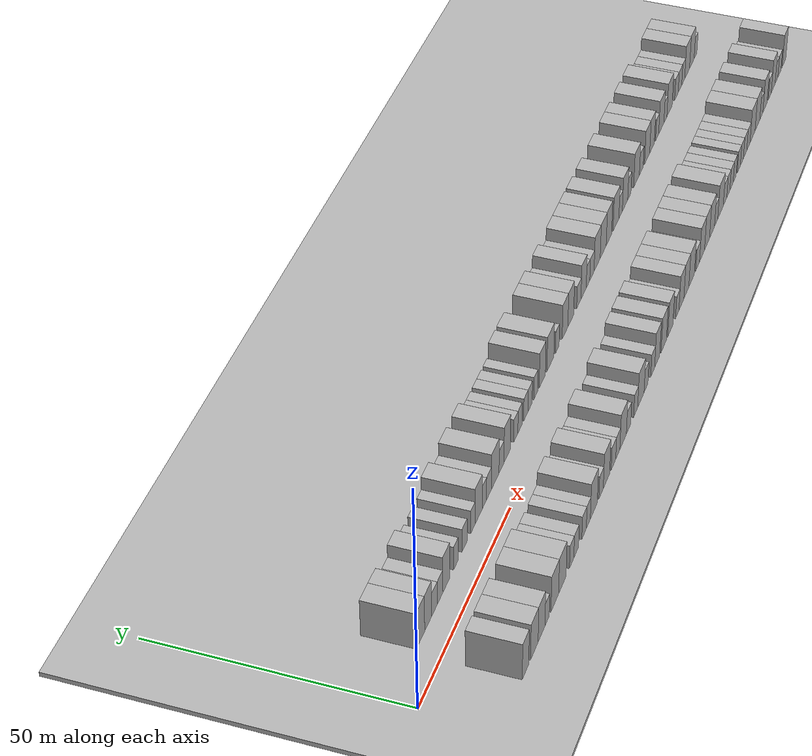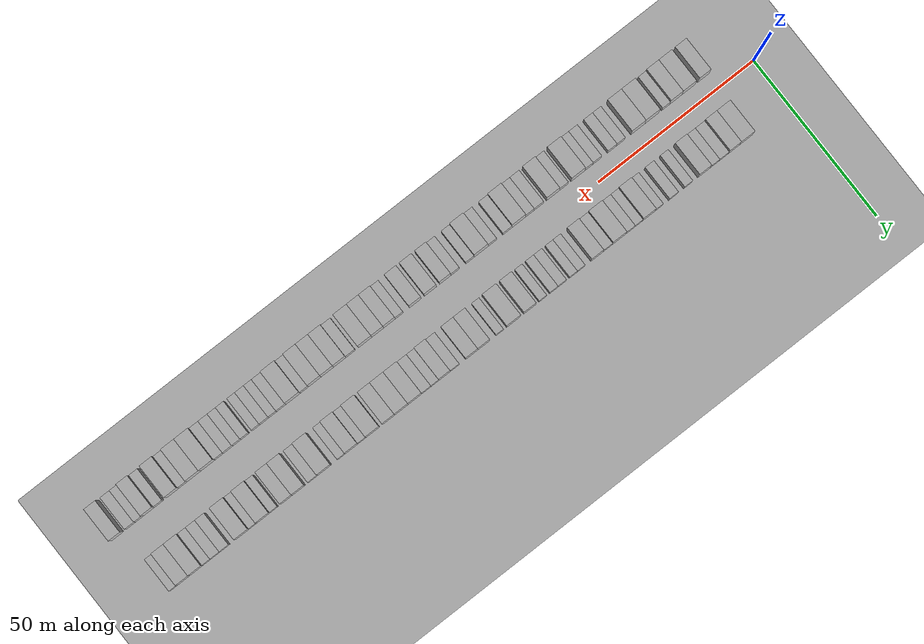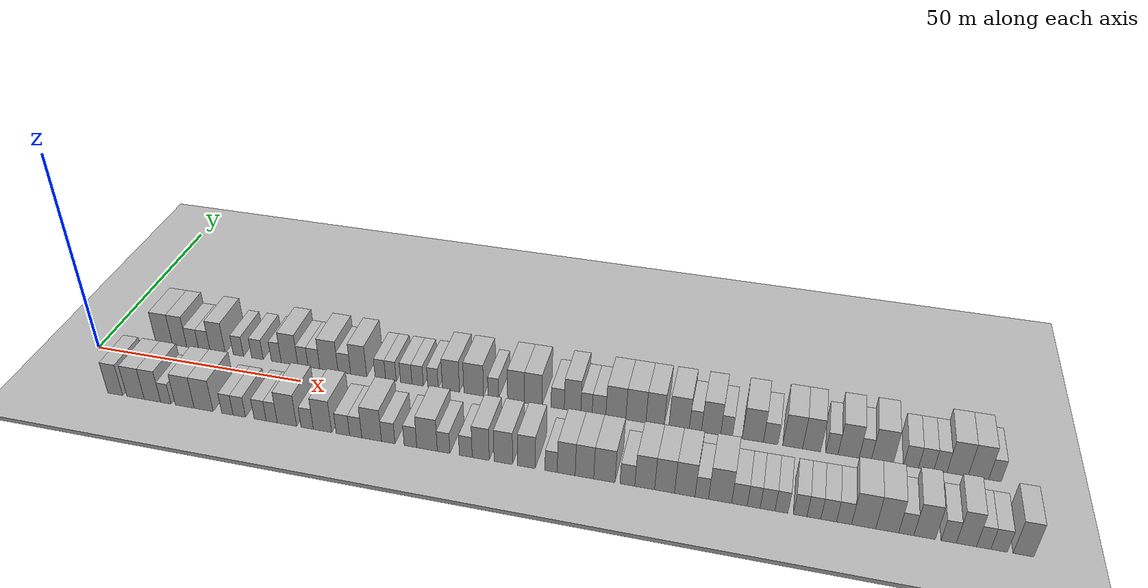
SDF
<?xml version="1.0" encoding="utf-8"?>

<sdf version="1.6">

   <world name="default">

      <gui fullscreen="0">

         <camera name="user_camera">

            <pose>-15 0 4.57585 0 0 0</pose>

            <view_controller>orbit</view_controller>

         </camera>

      </gui>

      <scene>

         <sky>

           <clouds>

             <speed>12</speed>

           </clouds>

         </sky>

         <ambient>0.4 0.4 0.4 1</ambient>

         <background>0.7 0.7 0.7 1</background>

         <shadows>1</shadows>

      </scene>

      <gravity>0 0 -9.8066</gravity>

      <magnetic_field>6e-06 2.3e-05 -4.2e-05</magnetic_field>

      <physics default="0" name="default_physics" type="ode">

         <ode>

            <solver>

               <type>quick</type>

               <iters>10</iters>

               <sor>1.0</sor>

               <use_dynamic_moi_rescaling>0</use_dynamic_moi_rescaling>

            </solver>

            <constraints>

               <cfm>0</cfm>

               <erp>0.2</erp>

               <contact_max_correcting_vel>100</contact_max_correcting_vel>

               <contact_surface_layer>0.001</contact_surface_layer>

            </constraints>

         </ode>

         <max_step_size>0.004</max_step_size>

         <real_time_factor>1</real_time_factor>

         <real_time_update_rate>250</real_time_update_rate>

      </physics>

      <light name="sun" type="directional">

         <cast_shadows>1</cast_shadows>

         <pose>0 0 10 0 0 0</pose>

         <diffuse>0.8 0.8 0.8 1</diffuse>

         <specular>0.2 0.2 0.2 1</specular>

         <attenuation>

            <range>1000</range>

            <constant>0.9</constant>

            <linear>0.01</linear>

            <quadratic>0.001</quadratic>

         </attenuation>

         <direction>-0.5 0.1 -0.9</direction>

      </light>

      <include>

         <name>ground_plane_1</name>

         <uri>model://HANNAS_ground_plane</uri>

         <pose>0 0 0  0 0 0</pose>

      </include>

      <include>

         <name>ground_plane_2</name>

         <uri>model://HANNAS_ground_plane</uri>

         <pose>100 0 0  0 0 0</pose>

      </include>

      <model name="building_1">

         <static>1</static>

         <pose frame="">14.1490 9.5000 0 0.000000 0.000000 1.570796</pose>

         <link name="link">

            <pose frame="">0 0 4.50 0 0 0</pose>

            <collision name="collision">

               <geometry>

                  <box>

                     <size>10.0000 4.2981 9.0000</size>

                  </box>

               </geometry>

               <max_contacts>10</max_contacts>

               <surface>

                  <contact>

                     <ode/>

                  </contact>

                  <bounce/>

                  <friction>

                     <torsional>

                        <ode/>

                     </torsional>

                     <ode/>

                  </friction>

               </surface>

            </collision>

            <visual name="visual">

               <cast_shadows>0</cast_shadows>

               <geometry>

                  <box>

                     <size>10.0000 4.2981 9.0000</size>

                  </box>

               </geometry>

               <material>

                  <script>

                     <uri>model://HANNAS_wall/materials/scripts</uri>

                     <uri>model://HANNAS_wall/materials/textures</uri>

                     <name>vrc/HANNAS_wall</name>

                  </script>

               </material>

            </visual>

            <self_collide>0</self_collide>

            <enable_wind>0</enable_wind>

            <kinematic>0</kinematic>

         </link>

      </model>

      <model name="building_2">

         <static>1</static>

         <pose frame="">18.1220 9.5000 0 0.000000 0.000000 1.570796</pose>

         <link name="link">

            <pose frame="">0 0 4.50 0 0 0</pose>

            <collision name="collision">

               <geometry>

                  <box>

                     <size>10.0000 3.6478 9.0000</size>

                  </box>

               </geometry>

               <max_contacts>10</max_contacts>

               <surface>

                  <contact>

                     <ode/>

                  </contact>

                  <bounce/>

                  <friction>

                     <torsional>

                        <ode/>

                     </torsional>

                     <ode/>

                  </friction>

               </surface>

            </collision>

            <visual name="visual">

               <cast_shadows>0</cast_shadows>

               <geometry>

                  <box>

                     <size>10.0000 3.6478 9.0000</size>

                  </box>

               </geometry>

               <material>

                  <script>

                     <uri>model://HANNAS_wall/materials/scripts</uri>

                     <uri>model://HANNAS_wall/materials/textures</uri>

                     <name>vrc/HANNAS_wall</name>

                  </script>

               </material>

            </visual>

            <self_collide>0</self_collide>

            <enable_wind>0</enable_wind>

            <kinematic>0</kinematic>

         </link>

      </model>

      <model name="building_3">

         <static>1</static>

         <pose frame="">21.4412 9.5000 0 0.000000 0.000000 1.570796</pose>

         <link name="link">

            <pose frame="">0 0 3.00 0 0 0</pose>

            <collision name="collision">

               <geometry>

                  <box>

                     <size>10.0000 2.9907 6.0000</size>

                  </box>

               </geometry>

               <max_contacts>10</max_contacts>

               <surface>

                  <contact>

                     <ode/>

                  </contact>

                  <bounce/>

                  <friction>

                     <torsional>

                        <ode/>

                     </torsional>

                     <ode/>

                  </friction>

               </surface>

            </collision>

            <visual name="visual">

               <cast_shadows>0</cast_shadows>

               <geometry>

                  <box>

                     <size>10.0000 2.9907 6.0000</size>

                  </box>

               </geometry>

               <material>

                  <script>

                     <uri>model://HANNAS_wall/materials/scripts</uri>

                     <uri>model://HANNAS_wall/materials/textures</uri>

                     <name>vrc/HANNAS_wall</name>

                  </script>

               </material>

            </visual>

            <self_collide>0</self_collide>

            <enable_wind>0</enable_wind>

            <kinematic>0</kinematic>

         </link>

      </model>

      <model name="building_4">

         <static>1</static>

         <pose frame="">24.3763 9.5000 0 0.000000 0.000000 1.570796</pose>

         <link name="link">

            <pose frame="">0 0 3.00 0 0 0</pose>

            <collision name="collision">

               <geometry>

                  <box>

                     <size>10.0000 2.8793 6.0000</size>

                  </box>

               </geometry>

               <max_contacts>10</max_contacts>

               <surface>

                  <contact>

                     <ode/>

                  </contact>

                  <bounce/>

                  <friction>

                     <torsional>

                        <ode/>

                     </torsional>

                     <ode/>

                  </friction>

               </surface>

            </collision>

            <visual name="visual">

               <cast_shadows>0</cast_shadows>

               <geometry>

                  <box>

                     <size>10.0000 2.8793 6.0000</size>

                  </box>

               </geometry>

               <material>

                  <script>

                     <uri>model://HANNAS_wall/materials/scripts</uri>

                     <uri>model://HANNAS_wall/materials/textures</uri>

                     <name>vrc/HANNAS_wall</name>

                  </script>

               </material>

            </visual>

            <self_collide>0</self_collide>

            <enable_wind>0</enable_wind>

            <kinematic>0</kinematic>

         </link>

      </model>

      <model name="building_5">

         <static>1</static>

         <pose frame="">27.7177 9.5000 0 0.000000 0.000000 1.570796</pose>

         <link name="link">

            <pose frame="">0 0 4.50 0 0 0</pose>

            <collision name="collision">

               <geometry>

                  <box>

                     <size>10.0000 3.8036 9.0000</size>

                  </box>

               </geometry>

               <max_contacts>10</max_contacts>

               <surface>

                  <contact>

                     <ode/>

                  </contact>

                  <bounce/>

                  <friction>

                     <torsional>

                        <ode/>

                     </torsional>

                     <ode/>

                  </friction>

               </surface>

            </collision>

            <visual name="visual">

               <cast_shadows>0</cast_shadows>

               <geometry>

                  <box>

                     <size>10.0000 3.8036 9.0000</size>

                  </box>

               </geometry>

               <material>

                  <script>

                     <uri>model://HANNAS_wall/materials/scripts</uri>

                     <uri>model://HANNAS_wall/materials/textures</uri>

                     <name>vrc/HANNAS_wall</name>

                  </script>

               </material>

            </visual>

            <self_collide>0</self_collide>

            <enable_wind>0</enable_wind>

            <kinematic>0</kinematic>

         </link>

      </model>

      <model name="building_6">

         <static>1</static>

         <pose frame="">32.9033 9.5000 0 0.000000 0.000000 1.570796</pose>

         <link name="link">

            <pose frame="">0 0 3.00 0 0 0</pose>

            <collision name="collision">

               <geometry>

                  <box>

                     <size>10.0000 2.5676 6.0000</size>

                  </box>

               </geometry>

               <max_contacts>10</max_contacts>

               <surface>

                  <contact>

                     <ode/>

                  </contact>

                  <bounce/>

                  <friction>

                     <torsional>

                        <ode/>

                     </torsional>

                     <ode/>

                  </friction>

               </surface>

            </collision>

            <visual name="visual">

               <cast_shadows>0</cast_shadows>

               <geometry>

                  <box>

                     <size>10.0000 2.5676 6.0000</size>

                  </box>

               </geometry>

               <material>

                  <script>

                     <uri>model://HANNAS_wall/materials/scripts</uri>

                     <uri>model://HANNAS_wall/materials/textures</uri>

                     <name>vrc/HANNAS_wall</name>

                  </script>

               </material>

            </visual>

            <self_collide>0</self_collide>

            <enable_wind>0</enable_wind>

            <kinematic>0</kinematic>

         </link>

      </model>

      <model name="building_7">

         <static>1</static>

         <pose frame="">37.6088 9.5000 0 0.000000 0.000000 1.570796</pose>

         <link name="link">

            <pose frame="">0 0 3.00 0 0 0</pose>

            <collision name="collision">

               <geometry>

                  <box>

                     <size>10.0000 2.8434 6.0000</size>

                  </box>

               </geometry>

               <max_contacts>10</max_contacts>

               <surface>

                  <contact>

                     <ode/>

                  </contact>

                  <bounce/>

                  <friction>

                     <torsional>

                        <ode/>

                     </torsional>

                     <ode/>

                  </friction>

               </surface>

            </collision>

            <visual name="visual">

               <cast_shadows>0</cast_shadows>

               <geometry>

                  <box>

                     <size>10.0000 2.8434 6.0000</size>

                  </box>

               </geometry>

               <material>

                  <script>

                     <uri>model://HANNAS_wall/materials/scripts</uri>

                     <uri>model://HANNAS_wall/materials/textures</uri>

                     <name>vrc/HANNAS_wall</name>

                  </script>

               </material>

            </visual>

            <self_collide>0</self_collide>

            <enable_wind>0</enable_wind>

            <kinematic>0</kinematic>

         </link>

      </model>

      <model name="building_8">

         <static>1</static>

         <pose frame="">42.2495 9.5000 0 0.000000 0.000000 1.570796</pose>

         <link name="link">

            <pose frame="">0 0 3.00 0 0 0</pose>

            <collision name="collision">

               <geometry>

                  <box>

                     <size>10.0000 2.4380 6.0000</size>

                  </box>

               </geometry>

               <max_contacts>10</max_contacts>

               <surface>

                  <contact>

                     <ode/>

                  </contact>

                  <bounce/>

                  <friction>

                     <torsional>

                        <ode/>

                     </torsional>

                     <ode/>

                  </friction>

               </surface>

            </collision>

            <visual name="visual">

               <cast_shadows>0</cast_shadows>

               <geometry>

                  <box>

                     <size>10.0000 2.4380 6.0000</size>

                  </box>

               </geometry>

               <material>

                  <script>

                     <uri>model://HANNAS_wall/materials/scripts</uri>

                     <uri>model://HANNAS_wall/materials/textures</uri>

                     <name>vrc/HANNAS_wall</name>

                  </script>

               </material>

            </visual>

            <self_collide>0</self_collide>

            <enable_wind>0</enable_wind>

            <kinematic>0</kinematic>

         </link>

      </model>

      <model name="building_9">

         <static>1</static>

         <pose frame="">45.4868 9.5000 0 0.000000 0.000000 1.570796</pose>

         <link name="link">

            <pose frame="">0 0 4.50 0 0 0</pose>

            <collision name="collision">

               <geometry>

                  <box>

                     <size>10.0000 4.0367 9.0000</size>

                  </box>

               </geometry>

               <max_contacts>10</max_contacts>

               <surface>

                  <contact>

                     <ode/>

                  </contact>

                  <bounce/>

                  <friction>

                     <torsional>

                        <ode/>

                     </torsional>

                     <ode/>

                  </friction>

               </surface>

            </collision>

            <visual name="visual">

               <cast_shadows>0</cast_shadows>

               <geometry>

                  <box>

                     <size>10.0000 4.0367 9.0000</size>

                  </box>

               </geometry>

               <material>

                  <script>

                     <uri>model://HANNAS_wall/materials/scripts</uri>

                     <uri>model://HANNAS_wall/materials/textures</uri>

                     <name>vrc/HANNAS_wall</name>

                  </script>

               </material>

            </visual>

            <self_collide>0</self_collide>

            <enable_wind>0</enable_wind>

            <kinematic>0</kinematic>

         </link>

      </model>

      <model name="building_10">

         <static>1</static>

         <pose frame="">48.7472 9.5000 0 0.000000 0.000000 1.570796</pose>

         <link name="link">

            <pose frame="">0 0 3.00 0 0 0</pose>

            <collision name="collision">

               <geometry>

                  <box>

                     <size>10.0000 2.4840 6.0000</size>

                  </box>

               </geometry>

               <max_contacts>10</max_contacts>

               <surface>

                  <contact>

                     <ode/>

                  </contact>

                  <bounce/>

                  <friction>

                     <torsional>

                        <ode/>

                     </torsional>

                     <ode/>

                  </friction>

               </surface>

            </collision>

            <visual name="visual">

               <cast_shadows>0</cast_shadows>

               <geometry>

                  <box>

                     <size>10.0000 2.4840 6.0000</size>

                  </box>

               </geometry>

               <material>

                  <script>

                     <uri>model://HANNAS_wall/materials/scripts</uri>

                     <uri>model://HANNAS_wall/materials/textures</uri>

                     <name>vrc/HANNAS_wall</name>

                  </script>

               </material>

            </visual>

            <self_collide>0</self_collide>

            <enable_wind>0</enable_wind>

            <kinematic>0</kinematic>

         </link>

      </model>

      <model name="building_11">

         <static>1</static>

         <pose frame="">51.4006 9.5000 0 0.000000 0.000000 1.570796</pose>

         <link name="link">

            <pose frame="">0 0 3.00 0 0 0</pose>

            <collision name="collision">

               <geometry>

                  <box>

                     <size>10.0000 2.8228 6.0000</size>

                  </box>

               </geometry>

               <max_contacts>10</max_contacts>

               <surface>

                  <contact>

                     <ode/>

                  </contact>

                  <bounce/>

                  <friction>

                     <torsional>

                        <ode/>

                     </torsional>

                     <ode/>

                  </friction>

               </surface>

            </collision>

            <visual name="visual">

               <cast_shadows>0</cast_shadows>

               <geometry>

                  <box>

                     <size>10.0000 2.8228 6.0000</size>

                  </box>

               </geometry>

               <material>

                  <script>

                     <uri>model://HANNAS_wall/materials/scripts</uri>

                     <uri>model://HANNAS_wall/materials/textures</uri>

                     <name>vrc/HANNAS_wall</name>

                  </script>

               </material>

            </visual>

            <self_collide>0</self_collide>

            <enable_wind>0</enable_wind>

            <kinematic>0</kinematic>

         </link>

      </model>

      <model name="building_12">

         <static>1</static>

         <pose frame="">55.0039 9.5000 0 0.000000 0.000000 1.570796</pose>

         <link name="link">

            <pose frame="">0 0 4.50 0 0 0</pose>

            <collision name="collision">

               <geometry>

                  <box>

                     <size>10.0000 4.3839 9.0000</size>

                  </box>

               </geometry>

               <max_contacts>10</max_contacts>

               <surface>

                  <contact>

                     <ode/>

                  </contact>

                  <bounce/>

                  <friction>

                     <torsional>

                        <ode/>

                     </torsional>

                     <ode/>

                  </friction>

               </surface>

            </collision>

            <visual name="visual">

               <cast_shadows>0</cast_shadows>

               <geometry>

                  <box>

                     <size>10.0000 4.3839 9.0000</size>

                  </box>

               </geometry>

               <material>

                  <script>

                     <uri>model://HANNAS_wall/materials/scripts</uri>

                     <uri>model://HANNAS_wall/materials/textures</uri>

                     <name>vrc/HANNAS_wall</name>

                  </script>

               </material>

            </visual>

            <self_collide>0</self_collide>

            <enable_wind>0</enable_wind>

            <kinematic>0</kinematic>

         </link>

      </model>

      <model name="building_13">

         <static>1</static>

         <pose frame="">58.6897 9.5000 0 0.000000 0.000000 1.570796</pose>

         <link name="link">

            <pose frame="">0 0 3.00 0 0 0</pose>

            <collision name="collision">

               <geometry>

                  <box>

                     <size>10.0000 2.9877 6.0000</size>

                  </box>

               </geometry>

               <max_contacts>10</max_contacts>

               <surface>

                  <contact>

                     <ode/>

                  </contact>

                  <bounce/>

                  <friction>

                     <torsional>

                        <ode/>

                     </torsional>

                     <ode/>

                  </friction>

               </surface>

            </collision>

            <visual name="visual">

               <cast_shadows>0</cast_shadows>

               <geometry>

                  <box>

                     <size>10.0000 2.9877 6.0000</size>

                  </box>

               </geometry>

               <material>

                  <script>

                     <uri>model://HANNAS_wall/materials/scripts</uri>

                     <uri>model://HANNAS_wall/materials/textures</uri>

                     <name>vrc/HANNAS_wall</name>

                  </script>

               </material>

            </visual>

            <self_collide>0</self_collide>

            <enable_wind>0</enable_wind>

            <kinematic>0</kinematic>

         </link>

      </model>

      <model name="building_14">

         <static>1</static>

         <pose frame="">62.0949 9.5000 0 0.000000 0.000000 1.570796</pose>

         <link name="link">

            <pose frame="">0 0 4.50 0 0 0</pose>

            <collision name="collision">

               <geometry>

                  <box>

                     <size>10.0000 3.8226 9.0000</size>

                  </box>

               </geometry>

               <max_contacts>10</max_contacts>

               <surface>

                  <contact>

                     <ode/>

                  </contact>

                  <bounce/>

                  <friction>

                     <torsional>

                        <ode/>

                     </torsional>

                     <ode/>

                  </friction>

               </surface>

            </collision>

            <visual name="visual">

               <cast_shadows>0</cast_shadows>

               <geometry>

                  <box>

                     <size>10.0000 3.8226 9.0000</size>

                  </box>

               </geometry>

               <material>

                  <script>

                     <uri>model://HANNAS_wall/materials/scripts</uri>

                     <uri>model://HANNAS_wall/materials/textures</uri>

                     <name>vrc/HANNAS_wall</name>

                  </script>

               </material>

            </visual>

            <self_collide>0</self_collide>

            <enable_wind>0</enable_wind>

            <kinematic>0</kinematic>

         </link>

      </model>

      <model name="building_15">

         <static>1</static>

         <pose frame="">67.2365 9.5000 0 0.000000 0.000000 1.570796</pose>

         <link name="link">

            <pose frame="">0 0 3.00 0 0 0</pose>

            <collision name="collision">

               <geometry>

                  <box>

                     <size>10.0000 2.4606 6.0000</size>

                  </box>

               </geometry>

               <max_contacts>10</max_contacts>

               <surface>

                  <contact>

                     <ode/>

                  </contact>

                  <bounce/>

                  <friction>

                     <torsional>

                        <ode/>

                     </torsional>

                     <ode/>

                  </friction>

               </surface>

            </collision>

            <visual name="visual">

               <cast_shadows>0</cast_shadows>

               <geometry>

                  <box>

                     <size>10.0000 2.4606 6.0000</size>

                  </box>

               </geometry>

               <material>

                  <script>

                     <uri>model://HANNAS_wall/materials/scripts</uri>

                     <uri>model://HANNAS_wall/materials/textures</uri>

                     <name>vrc/HANNAS_wall</name>

                  </script>

               </material>

            </visual>

            <self_collide>0</self_collide>

            <enable_wind>0</enable_wind>

            <kinematic>0</kinematic>

         </link>

      </model>

      <model name="building_16">

         <static>1</static>

         <pose frame="">69.7130 9.5000 0 0.000000 0.000000 1.570796</pose>

         <link name="link">

            <pose frame="">0 0 3.00 0 0 0</pose>

            <collision name="collision">

               <geometry>

                  <box>

                     <size>10.0000 2.4924 6.0000</size>

                  </box>

               </geometry>

               <max_contacts>10</max_contacts>

               <surface>

                  <contact>

                     <ode/>

                  </contact>

                  <bounce/>

                  <friction>

                     <torsional>

                        <ode/>

                     </torsional>

                     <ode/>

                  </friction>

               </surface>

            </collision>

            <visual name="visual">

               <cast_shadows>0</cast_shadows>

               <geometry>

                  <box>

                     <size>10.0000 2.4924 6.0000</size>

                  </box>

               </geometry>

               <material>

                  <script>

                     <uri>model://HANNAS_wall/materials/scripts</uri>

                     <uri>model://HANNAS_wall/materials/textures</uri>

                     <name>vrc/HANNAS_wall</name>

                  </script>

               </material>

            </visual>

            <self_collide>0</self_collide>

            <enable_wind>0</enable_wind>

            <kinematic>0</kinematic>

         </link>

      </model>

      <model name="building_17">

         <static>1</static>

         <pose frame="">73.2931 9.5000 0 0.000000 0.000000 1.570796</pose>

         <link name="link">

            <pose frame="">0 0 3.00 0 0 0</pose>

            <collision name="collision">

               <geometry>

                  <box>

                     <size>10.0000 2.6680 6.0000</size>

                  </box>

               </geometry>

               <max_contacts>10</max_contacts>

               <surface>

                  <contact>

                     <ode/>

                  </contact>

                  <bounce/>

                  <friction>

                     <torsional>

                        <ode/>

                     </torsional>

                     <ode/>

                  </friction>

               </surface>

            </collision>

            <visual name="visual">

               <cast_shadows>0</cast_shadows>

               <geometry>

                  <box>

                     <size>10.0000 2.6680 6.0000</size>

                  </box>

               </geometry>

               <material>

                  <script>

                     <uri>model://HANNAS_wall/materials/scripts</uri>

                     <uri>model://HANNAS_wall/materials/textures</uri>

                     <name>vrc/HANNAS_wall</name>

                  </script>

               </material>

            </visual>

            <self_collide>0</self_collide>

            <enable_wind>0</enable_wind>

            <kinematic>0</kinematic>

         </link>

      </model>

      <model name="building_18">

         <static>1</static>

         <pose frame="">75.9414 9.5000 0 0.000000 0.000000 1.570796</pose>

         <link name="link">

            <pose frame="">0 0 3.00 0 0 0</pose>

            <collision name="collision">

               <geometry>

                  <box>

                     <size>10.0000 2.6286 6.0000</size>

                  </box>

               </geometry>

               <max_contacts>10</max_contacts>

               <surface>

                  <contact>

                     <ode/>

                  </contact>

                  <bounce/>

                  <friction>

                     <torsional>

                        <ode/>

                     </torsional>

                     <ode/>

                  </friction>

               </surface>

            </collision>

            <visual name="visual">

               <cast_shadows>0</cast_shadows>

               <geometry>

                  <box>

                     <size>10.0000 2.6286 6.0000</size>

                  </box>

               </geometry>

               <material>

                  <script>

                     <uri>model://HANNAS_wall/materials/scripts</uri>

                     <uri>model://HANNAS_wall/materials/textures</uri>

                     <name>vrc/HANNAS_wall</name>

                  </script>

               </material>

            </visual>

            <self_collide>0</self_collide>

            <enable_wind>0</enable_wind>

            <kinematic>0</kinematic>

         </link>

      </model>

      <model name="building_19">

         <static>1</static>

         <pose frame="">79.4634 9.5000 0 0.000000 0.000000 1.570796</pose>

         <link name="link">

            <pose frame="">0 0 3.00 0 0 0</pose>

            <collision name="collision">

               <geometry>

                  <box>

                     <size>10.0000 2.4155 6.0000</size>

                  </box>

               </geometry>

               <max_contacts>10</max_contacts>

               <surface>

                  <contact>

                     <ode/>

                  </contact>

                  <bounce/>

                  <friction>

                     <torsional>

                        <ode/>

                     </torsional>

                     <ode/>

                  </friction>

               </surface>

            </collision>

            <visual name="visual">

               <cast_shadows>0</cast_shadows>

               <geometry>

                  <box>

                     <size>10.0000 2.4155 6.0000</size>

                  </box>

               </geometry>

               <material>

                  <script>

                     <uri>model://HANNAS_wall/materials/scripts</uri>

                     <uri>model://HANNAS_wall/materials/textures</uri>

                     <name>vrc/HANNAS_wall</name>

                  </script>

               </material>

            </visual>

            <self_collide>0</self_collide>

            <enable_wind>0</enable_wind>

            <kinematic>0</kinematic>

         </link>

      </model>

      <model name="building_20">

         <static>1</static>

         <pose frame="">83.6192 9.5000 0 0.000000 0.000000 1.570796</pose>

         <link name="link">

            <pose frame="">0 0 4.50 0 0 0</pose>

            <collision name="collision">

               <geometry>

                  <box>

                     <size>10.0000 3.8961 9.0000</size>

                  </box>

               </geometry>

               <max_contacts>10</max_contacts>

               <surface>

                  <contact>

                     <ode/>

                  </contact>

                  <bounce/>

                  <friction>

                     <torsional>

                        <ode/>

                     </torsional>

                     <ode/>

                  </friction>

               </surface>

            </collision>

            <visual name="visual">

               <cast_shadows>0</cast_shadows>

               <geometry>

                  <box>

                     <size>10.0000 3.8961 9.0000</size>

                  </box>

               </geometry>

               <material>

                  <script>

                     <uri>model://HANNAS_wall/materials/scripts</uri>

                     <uri>model://HANNAS_wall/materials/textures</uri>

                     <name>vrc/HANNAS_wall</name>

                  </script>

               </material>

            </visual>

            <self_collide>0</self_collide>

            <enable_wind>0</enable_wind>

            <kinematic>0</kinematic>

         </link>

      </model>

      <model name="building_21">

         <static>1</static>

         <pose frame="">88.8030 9.5000 0 0.000000 0.000000 1.570796</pose>

         <link name="link">

            <pose frame="">0 0 4.50 0 0 0</pose>

            <collision name="collision">

               <geometry>

                  <box>

                     <size>10.0000 4.4713 9.0000</size>

                  </box>

               </geometry>

               <max_contacts>10</max_contacts>

               <surface>

                  <contact>

                     <ode/>

                  </contact>

                  <bounce/>

                  <friction>

                     <torsional>

                        <ode/>

                     </torsional>

                     <ode/>

                  </friction>

               </surface>

            </collision>

            <visual name="visual">

               <cast_shadows>0</cast_shadows>

               <geometry>

                  <box>

                     <size>10.0000 4.4713 9.0000</size>

                  </box>

               </geometry>

               <material>

                  <script>

                     <uri>model://HANNAS_wall/materials/scripts</uri>

                     <uri>model://HANNAS_wall/materials/textures</uri>

                     <name>vrc/HANNAS_wall</name>

                  </script>

               </material>

            </visual>

            <self_collide>0</self_collide>

            <enable_wind>0</enable_wind>

            <kinematic>0</kinematic>

         </link>

      </model>

      <model name="building_22">

         <static>1</static>

         <pose frame="">93.2414 9.5000 0 0.000000 0.000000 1.570796</pose>

         <link name="link">

            <pose frame="">0 0 3.00 0 0 0</pose>

            <collision name="collision">

               <geometry>

                  <box>

                     <size>10.0000 2.4057 6.0000</size>

                  </box>

               </geometry>

               <max_contacts>10</max_contacts>

               <surface>

                  <contact>

                     <ode/>

                  </contact>

                  <bounce/>

                  <friction>

                     <torsional>

                        <ode/>

                     </torsional>

                     <ode/>

                  </friction>

               </surface>

            </collision>

            <visual name="visual">

               <cast_shadows>0</cast_shadows>

               <geometry>

                  <box>

                     <size>10.0000 2.4057 6.0000</size>

                  </box>

               </geometry>

               <material>

                  <script>

                     <uri>model://HANNAS_wall/materials/scripts</uri>

                     <uri>model://HANNAS_wall/materials/textures</uri>

                     <name>vrc/HANNAS_wall</name>

                  </script>

               </material>

            </visual>

            <self_collide>0</self_collide>

            <enable_wind>0</enable_wind>

            <kinematic>0</kinematic>

         </link>

      </model>

      <model name="building_23">

         <static>1</static>

         <pose frame="">98.3310 9.5000 0 0.000000 0.000000 1.570796</pose>

         <link name="link">

            <pose frame="">0 0 4.50 0 0 0</pose>

            <collision name="collision">

               <geometry>

                  <box>

                     <size>10.0000 3.7735 9.0000</size>

                  </box>

               </geometry>

               <max_contacts>10</max_contacts>

               <surface>

                  <contact>

                     <ode/>

                  </contact>

                  <bounce/>

                  <friction>

                     <torsional>

                        <ode/>

                     </torsional>

                     <ode/>

                  </friction>

               </surface>

            </collision>

            <visual name="visual">

               <cast_shadows>0</cast_shadows>

               <geometry>

                  <box>

                     <size>10.0000 3.7735 9.0000</size>

                  </box>

               </geometry>

               <material>

                  <script>

                     <uri>model://HANNAS_wall/materials/scripts</uri>

                     <uri>model://HANNAS_wall/materials/textures</uri>

                     <name>vrc/HANNAS_wall</name>

                  </script>

               </material>

            </visual>

            <self_collide>0</self_collide>

            <enable_wind>0</enable_wind>

            <kinematic>0</kinematic>

         </link>

      </model>

      <model name="building_24">

         <static>1</static>

         <pose frame="">102.1723 9.5000 0 0.000000 0.000000 1.570796</pose>

         <link name="link">

            <pose frame="">0 0 4.50 0 0 0</pose>

            <collision name="collision">

               <geometry>

                  <box>

                     <size>10.0000 3.9090 9.0000</size>

                  </box>

               </geometry>

               <max_contacts>10</max_contacts>

               <surface>

                  <contact>

                     <ode/>

                  </contact>

                  <bounce/>

                  <friction>

                     <torsional>

                        <ode/>

                     </torsional>

                     <ode/>

                  </friction>

               </surface>

            </collision>

            <visual name="visual">

               <cast_shadows>0</cast_shadows>

               <geometry>

                  <box>

                     <size>10.0000 3.9090 9.0000</size>

                  </box>

               </geometry>

               <material>

                  <script>

                     <uri>model://HANNAS_wall/materials/scripts</uri>

                     <uri>model://HANNAS_wall/materials/textures</uri>

                     <name>vrc/HANNAS_wall</name>

                  </script>

               </material>

            </visual>

            <self_collide>0</self_collide>

            <enable_wind>0</enable_wind>

            <kinematic>0</kinematic>

         </link>

      </model>

      <model name="building_25">

         <static>1</static>

         <pose frame="">107.5789 9.5000 0 0.000000 0.000000 1.570796</pose>

         <link name="link">

            <pose frame="">0 0 3.00 0 0 0</pose>

            <collision name="collision">

               <geometry>

                  <box>

                     <size>10.0000 2.9042 6.0000</size>

                  </box>

               </geometry>

               <max_contacts>10</max_contacts>

               <surface>

                  <contact>

                     <ode/>

                  </contact>

                  <bounce/>

                  <friction>

                     <torsional>

                        <ode/>

                     </torsional>

                     <ode/>

                  </friction>

               </surface>

            </collision>

            <visual name="visual">

               <cast_shadows>0</cast_shadows>

               <geometry>

                  <box>

                     <size>10.0000 2.9042 6.0000</size>

                  </box>

               </geometry>

               <material>

                  <script>

                     <uri>model://HANNAS_wall/materials/scripts</uri>

                     <uri>model://HANNAS_wall/materials/textures</uri>

                     <name>vrc/HANNAS_wall</name>

                  </script>

               </material>

            </visual>

            <self_collide>0</self_collide>

            <enable_wind>0</enable_wind>

            <kinematic>0</kinematic>

         </link>

      </model>

      <model name="building_26">

         <static>1</static>

         <pose frame="">110.8466 9.5000 0 0.000000 0.000000 1.570796</pose>

         <link name="link">

            <pose frame="">0 0 4.50 0 0 0</pose>

            <collision name="collision">

               <geometry>

                  <box>

                     <size>10.0000 3.6311 9.0000</size>

                  </box>

               </geometry>

               <max_contacts>10</max_contacts>

               <surface>

                  <contact>

                     <ode/>

                  </contact>

                  <bounce/>

                  <friction>

                     <torsional>

                        <ode/>

                     </torsional>

                     <ode/>

                  </friction>

               </surface>

            </collision>

            <visual name="visual">

               <cast_shadows>0</cast_shadows>

               <geometry>

                  <box>

                     <size>10.0000 3.6311 9.0000</size>

                  </box>

               </geometry>

               <material>

                  <script>

                     <uri>model://HANNAS_wall/materials/scripts</uri>

                     <uri>model://HANNAS_wall/materials/textures</uri>

                     <name>vrc/HANNAS_wall</name>

                  </script>

               </material>

            </visual>

            <self_collide>0</self_collide>

            <enable_wind>0</enable_wind>

            <kinematic>0</kinematic>

         </link>

      </model>

      <model name="building_27">

         <static>1</static>

         <pose frame="">113.8942 9.5000 0 0.000000 0.000000 1.570796</pose>

         <link name="link">

            <pose frame="">0 0 3.00 0 0 0</pose>

            <collision name="collision">

               <geometry>

                  <box>

                     <size>10.0000 2.4641 6.0000</size>

                  </box>

               </geometry>

               <max_contacts>10</max_contacts>

               <surface>

                  <contact>

                     <ode/>

                  </contact>

                  <bounce/>

                  <friction>

                     <torsional>

                        <ode/>

                     </torsional>

                     <ode/>

                  </friction>

               </surface>

            </collision>

            <visual name="visual">

               <cast_shadows>0</cast_shadows>

               <geometry>

                  <box>

                     <size>10.0000 2.4641 6.0000</size>

                  </box>

               </geometry>

               <material>

                  <script>

                     <uri>model://HANNAS_wall/materials/scripts</uri>

                     <uri>model://HANNAS_wall/materials/textures</uri>

                     <name>vrc/HANNAS_wall</name>

                  </script>

               </material>

            </visual>

            <self_collide>0</self_collide>

            <enable_wind>0</enable_wind>

            <kinematic>0</kinematic>

         </link>

      </model>

      <model name="building_28">

         <static>1</static>

         <pose frame="">116.6158 9.5000 0 0.000000 0.000000 1.570796</pose>

         <link name="link">

            <pose frame="">0 0 3.00 0 0 0</pose>

            <collision name="collision">

               <geometry>

                  <box>

                     <size>10.0000 2.9791 6.0000</size>

                  </box>

               </geometry>

               <max_contacts>10</max_contacts>

               <surface>

                  <contact>

                     <ode/>

                  </contact>

                  <bounce/>

                  <friction>

                     <torsional>

                        <ode/>

                     </torsional>

                     <ode/>

                  </friction>

               </surface>

            </collision>

            <visual name="visual">

               <cast_shadows>0</cast_shadows>

               <geometry>

                  <box>

                     <size>10.0000 2.9791 6.0000</size>

                  </box>

               </geometry>

               <material>

                  <script>

                     <uri>model://HANNAS_wall/materials/scripts</uri>

                     <uri>model://HANNAS_wall/materials/textures</uri>

                     <name>vrc/HANNAS_wall</name>

                  </script>

               </material>

            </visual>

            <self_collide>0</self_collide>

            <enable_wind>0</enable_wind>

            <kinematic>0</kinematic>

         </link>

      </model>

      <model name="building_29">

         <static>1</static>

         <pose frame="">120.2576 9.5000 0 0.000000 0.000000 1.570796</pose>

         <link name="link">

            <pose frame="">0 0 4.50 0 0 0</pose>

            <collision name="collision">

               <geometry>

                  <box>

                     <size>10.0000 4.3044 9.0000</size>

                  </box>

               </geometry>

               <max_contacts>10</max_contacts>

               <surface>

                  <contact>

                     <ode/>

                  </contact>

                  <bounce/>

                  <friction>

                     <torsional>

                        <ode/>

                     </torsional>

                     <ode/>

                  </friction>

               </surface>

            </collision>

            <visual name="visual">

               <cast_shadows>0</cast_shadows>

               <geometry>

                  <box>

                     <size>10.0000 4.3044 9.0000</size>

                  </box>

               </geometry>

               <material>

                  <script>

                     <uri>model://HANNAS_wall/materials/scripts</uri>

                     <uri>model://HANNAS_wall/materials/textures</uri>

                     <name>vrc/HANNAS_wall</name>

                  </script>

               </material>

            </visual>

            <self_collide>0</self_collide>

            <enable_wind>0</enable_wind>

            <kinematic>0</kinematic>

         </link>

      </model>

      <model name="building_30">

         <static>1</static>

         <pose frame="">124.5517 9.5000 0 0.000000 0.000000 1.570796</pose>

         <link name="link">

            <pose frame="">0 0 4.50 0 0 0</pose>

            <collision name="collision">

               <geometry>

                  <box>

                     <size>10.0000 4.2838 9.0000</size>

                  </box>

               </geometry>

               <max_contacts>10</max_contacts>

               <surface>

                  <contact>

                     <ode/>

                  </contact>

                  <bounce/>

                  <friction>

                     <torsional>

                        <ode/>

                     </torsional>

                     <ode/>

                  </friction>

               </surface>

            </collision>

            <visual name="visual">

               <cast_shadows>0</cast_shadows>

               <geometry>

                  <box>

                     <size>10.0000 4.2838 9.0000</size>

                  </box>

               </geometry>

               <material>

                  <script>

                     <uri>model://HANNAS_wall/materials/scripts</uri>

                     <uri>model://HANNAS_wall/materials/textures</uri>

                     <name>vrc/HANNAS_wall</name>

                  </script>

               </material>

            </visual>

            <self_collide>0</self_collide>

            <enable_wind>0</enable_wind>

            <kinematic>0</kinematic>

         </link>

      </model>

      <model name="building_31">

         <static>1</static>

         <pose frame="">128.6397 9.5000 0 0.000000 0.000000 1.570796</pose>

         <link name="link">

            <pose frame="">0 0 4.50 0 0 0</pose>

            <collision name="collision">

               <geometry>

                  <box>

                     <size>10.0000 3.8923 9.0000</size>

                  </box>

               </geometry>

               <max_contacts>10</max_contacts>

               <surface>

                  <contact>

                     <ode/>

                  </contact>

                  <bounce/>

                  <friction>

                     <torsional>

                        <ode/>

                     </torsional>

                     <ode/>

                  </friction>

               </surface>

            </collision>

            <visual name="visual">

               <cast_shadows>0</cast_shadows>

               <geometry>

                  <box>

                     <size>10.0000 3.8923 9.0000</size>

                  </box>

               </geometry>

               <material>

                  <script>

                     <uri>model://HANNAS_wall/materials/scripts</uri>

                     <uri>model://HANNAS_wall/materials/textures</uri>

                     <name>vrc/HANNAS_wall</name>

                  </script>

               </material>

            </visual>

            <self_collide>0</self_collide>

            <enable_wind>0</enable_wind>

            <kinematic>0</kinematic>

         </link>

      </model>

      <model name="building_32">

         <static>1</static>

         <pose frame="">133.7341 9.5000 0 0.000000 0.000000 1.570796</pose>

         <link name="link">

            <pose frame="">0 0 4.50 0 0 0</pose>

            <collision name="collision">

               <geometry>

                  <box>

                     <size>10.0000 4.2966 9.0000</size>

                  </box>

               </geometry>

               <max_contacts>10</max_contacts>

               <surface>

                  <contact>

                     <ode/>

                  </contact>

                  <bounce/>

                  <friction>

                     <torsional>

                        <ode/>

                     </torsional>

                     <ode/>

                  </friction>

               </surface>

            </collision>

            <visual name="visual">

               <cast_shadows>0</cast_shadows>

               <geometry>

                  <box>

                     <size>10.0000 4.2966 9.0000</size>

                  </box>

               </geometry>

               <material>

                  <script>

                     <uri>model://HANNAS_wall/materials/scripts</uri>

                     <uri>model://HANNAS_wall/materials/textures</uri>

                     <name>vrc/HANNAS_wall</name>

                  </script>

               </material>

            </visual>

            <self_collide>0</self_collide>

            <enable_wind>0</enable_wind>

            <kinematic>0</kinematic>

         </link>

      </model>

      <model name="building_33">

         <static>1</static>

         <pose frame="">137.1597 9.5000 0 0.000000 0.000000 1.570796</pose>

         <link name="link">

            <pose frame="">0 0 3.00 0 0 0</pose>

            <collision name="collision">

               <geometry>

                  <box>

                     <size>10.0000 2.5544 6.0000</size>

                  </box>

               </geometry>

               <max_contacts>10</max_contacts>

               <surface>

                  <contact>

                     <ode/>

                  </contact>

                  <bounce/>

                  <friction>

                     <torsional>

                        <ode/>

                     </torsional>

                     <ode/>

                  </friction>

               </surface>

            </collision>

            <visual name="visual">

               <cast_shadows>0</cast_shadows>

               <geometry>

                  <box>

                     <size>10.0000 2.5544 6.0000</size>

                  </box>

               </geometry>

               <material>

                  <script>

                     <uri>model://HANNAS_wall/materials/scripts</uri>

                     <uri>model://HANNAS_wall/materials/textures</uri>

                     <name>vrc/HANNAS_wall</name>

                  </script>

               </material>

            </visual>

            <self_collide>0</self_collide>

            <enable_wind>0</enable_wind>

            <kinematic>0</kinematic>

         </link>

      </model>

      <model name="building_34">

         <static>1</static>

         <pose frame="">140.4432 9.5000 0 0.000000 0.000000 1.570796</pose>

         <link name="link">

            <pose frame="">0 0 4.50 0 0 0</pose>

            <collision name="collision">

               <geometry>

                  <box>

                     <size>10.0000 4.0127 9.0000</size>

                  </box>

               </geometry>

               <max_contacts>10</max_contacts>

               <surface>

                  <contact>

                     <ode/>

                  </contact>

                  <bounce/>

                  <friction>

                     <torsional>

                        <ode/>

                     </torsional>

                     <ode/>

                  </friction>

               </surface>

            </collision>

            <visual name="visual">

               <cast_shadows>0</cast_shadows>

               <geometry>

                  <box>

                     <size>10.0000 4.0127 9.0000</size>

                  </box>

               </geometry>

               <material>

                  <script>

                     <uri>model://HANNAS_wall/materials/scripts</uri>

                     <uri>model://HANNAS_wall/materials/textures</uri>

                     <name>vrc/HANNAS_wall</name>

                  </script>

               </material>

            </visual>

            <self_collide>0</self_collide>

            <enable_wind>0</enable_wind>

            <kinematic>0</kinematic>

         </link>

      </model>

      <model name="building_35">

         <static>1</static>

         <pose frame="">143.6818 9.5000 0 0.000000 0.000000 1.570796</pose>

         <link name="link">

            <pose frame="">0 0 3.00 0 0 0</pose>

            <collision name="collision">

               <geometry>

                  <box>

                     <size>10.0000 2.4644 6.0000</size>

                  </box>

               </geometry>

               <max_contacts>10</max_contacts>

               <surface>

                  <contact>

                     <ode/>

                  </contact>

                  <bounce/>

                  <friction>

                     <torsional>

                        <ode/>

                     </torsional>

                     <ode/>

                  </friction>

               </surface>

            </collision>

            <visual name="visual">

               <cast_shadows>0</cast_shadows>

               <geometry>

                  <box>

                     <size>10.0000 2.4644 6.0000</size>

                  </box>

               </geometry>

               <material>

                  <script>

                     <uri>model://HANNAS_wall/materials/scripts</uri>

                     <uri>model://HANNAS_wall/materials/textures</uri>

                     <name>vrc/HANNAS_wall</name>

                  </script>

               </material>

            </visual>

            <self_collide>0</self_collide>

            <enable_wind>0</enable_wind>

            <kinematic>0</kinematic>

         </link>

      </model>

      <model name="building_36">

         <static>1</static>

         <pose frame="">149.0843 9.5000 0 0.000000 0.000000 1.570796</pose>

         <link name="link">

            <pose frame="">0 0 4.50 0 0 0</pose>

            <collision name="collision">

               <geometry>

                  <box>

                     <size>10.0000 4.3407 9.0000</size>

                  </box>

               </geometry>

               <max_contacts>10</max_contacts>

               <surface>

                  <contact>

                     <ode/>

                  </contact>

                  <bounce/>

                  <friction>

                     <torsional>

                        <ode/>

                     </torsional>

                     <ode/>

                  </friction>

               </surface>

            </collision>

            <visual name="visual">

               <cast_shadows>0</cast_shadows>

               <geometry>

                  <box>

                     <size>10.0000 4.3407 9.0000</size>

                  </box>

               </geometry>

               <material>

                  <script>

                     <uri>model://HANNAS_wall/materials/scripts</uri>

                     <uri>model://HANNAS_wall/materials/textures</uri>

                     <name>vrc/HANNAS_wall</name>

                  </script>

               </material>

            </visual>

            <self_collide>0</self_collide>

            <enable_wind>0</enable_wind>

            <kinematic>0</kinematic>

         </link>

      </model>

      <model name="building_37">

         <static>1</static>

         <pose frame="">152.7458 9.5000 0 0.000000 0.000000 1.570796</pose>

         <link name="link">

            <pose frame="">0 0 3.00 0 0 0</pose>

            <collision name="collision">

               <geometry>

                  <box>

                     <size>10.0000 2.9823 6.0000</size>

                  </box>

               </geometry>

               <max_contacts>10</max_contacts>

               <surface>

                  <contact>

                     <ode/>

                  </contact>

                  <bounce/>

                  <friction>

                     <torsional>

                        <ode/>

                     </torsional>

                     <ode/>

                  </friction>

               </surface>

            </collision>

            <visual name="visual">

               <cast_shadows>0</cast_shadows>

               <geometry>

                  <box>

                     <size>10.0000 2.9823 6.0000</size>

                  </box>

               </geometry>

               <material>

                  <script>

                     <uri>model://HANNAS_wall/materials/scripts</uri>

                     <uri>model://HANNAS_wall/materials/textures</uri>

                     <name>vrc/HANNAS_wall</name>

                  </script>

               </material>

            </visual>

            <self_collide>0</self_collide>

            <enable_wind>0</enable_wind>

            <kinematic>0</kinematic>

         </link>

      </model>

      <model name="building_38">

         <static>1</static>

         <pose frame="">157.2370 9.5000 0 0.000000 0.000000 1.570796</pose>

         <link name="link">

            <pose frame="">0 0 4.50 0 0 0</pose>

            <collision name="collision">

               <geometry>

                  <box>

                     <size>10.0000 4.0002 9.0000</size>

                  </box>

               </geometry>

               <max_contacts>10</max_contacts>

               <surface>

                  <contact>

                     <ode/>

                  </contact>

                  <bounce/>

                  <friction>

                     <torsional>

                        <ode/>

                     </torsional>

                     <ode/>

                  </friction>

               </surface>

            </collision>

            <visual name="visual">

               <cast_shadows>0</cast_shadows>

               <geometry>

                  <box>

                     <size>10.0000 4.0002 9.0000</size>

                  </box>

               </geometry>

               <material>

                  <script>

                     <uri>model://HANNAS_wall/materials/scripts</uri>

                     <uri>model://HANNAS_wall/materials/textures</uri>

                     <name>vrc/HANNAS_wall</name>

                  </script>

               </material>

            </visual>

            <self_collide>0</self_collide>

            <enable_wind>0</enable_wind>

            <kinematic>0</kinematic>

         </link>

      </model>

      <model name="building_39">

         <static>1</static>

         <pose frame="">161.0591 9.5000 0 0.000000 0.000000 1.570796</pose>

         <link name="link">

            <pose frame="">0 0 4.50 0 0 0</pose>

            <collision name="collision">

               <geometry>

                  <box>

                     <size>10.0000 3.6440 9.0000</size>

                  </box>

               </geometry>

               <max_contacts>10</max_contacts>

               <surface>

                  <contact>

                     <ode/>

                  </contact>

                  <bounce/>

                  <friction>

                     <torsional>

                        <ode/>

                     </torsional>

                     <ode/>

                  </friction>

               </surface>

            </collision>

            <visual name="visual">

               <cast_shadows>0</cast_shadows>

               <geometry>

                  <box>

                     <size>10.0000 3.6440 9.0000</size>

                  </box>

               </geometry>

               <material>

                  <script>

                     <uri>model://HANNAS_wall/materials/scripts</uri>

                     <uri>model://HANNAS_wall/materials/textures</uri>

                     <name>vrc/HANNAS_wall</name>

                  </script>

               </material>

            </visual>

            <self_collide>0</self_collide>

            <enable_wind>0</enable_wind>

            <kinematic>0</kinematic>

         </link>

      </model>

      <model name="building_40">

         <static>1</static>

         <pose frame="">165.1144 9.5000 0 0.000000 0.000000 1.570796</pose>

         <link name="link">

            <pose frame="">0 0 3.00 0 0 0</pose>

            <collision name="collision">

               <geometry>

                  <box>

                     <size>10.0000 2.4667 6.0000</size>

                  </box>

               </geometry>

               <max_contacts>10</max_contacts>

               <surface>

                  <contact>

                     <ode/>

                  </contact>

                  <bounce/>

                  <friction>

                     <torsional>

                        <ode/>

                     </torsional>

                     <ode/>

                  </friction>

               </surface>

            </collision>

            <visual name="visual">

               <cast_shadows>0</cast_shadows>

               <geometry>

                  <box>

                     <size>10.0000 2.4667 6.0000</size>

                  </box>

               </geometry>

               <material>

                  <script>

                     <uri>model://HANNAS_wall/materials/scripts</uri>

                     <uri>model://HANNAS_wall/materials/textures</uri>

                     <name>vrc/HANNAS_wall</name>

                  </script>

               </material>

            </visual>

            <self_collide>0</self_collide>

            <enable_wind>0</enable_wind>

            <kinematic>0</kinematic>

         </link>

      </model>

      <model name="building_41">

         <static>1</static>

         <pose frame="">168.4434 9.5000 0 0.000000 0.000000 1.570796</pose>

         <link name="link">

            <pose frame="">0 0 4.50 0 0 0</pose>

            <collision name="collision">

               <geometry>

                  <box>

                     <size>10.0000 4.1913 9.0000</size>

                  </box>

               </geometry>

               <max_contacts>10</max_contacts>

               <surface>

                  <contact>

                     <ode/>

                  </contact>

                  <bounce/>

                  <friction>

                     <torsional>

                        <ode/>

                     </torsional>

                     <ode/>

                  </friction>

               </surface>

            </collision>

            <visual name="visual">

               <cast_shadows>0</cast_shadows>

               <geometry>

                  <box>

                     <size>10.0000 4.1913 9.0000</size>

                  </box>

               </geometry>

               <material>

                  <script>

                     <uri>model://HANNAS_wall/materials/scripts</uri>

                     <uri>model://HANNAS_wall/materials/textures</uri>

                     <name>vrc/HANNAS_wall</name>

                  </script>

               </material>

            </visual>

            <self_collide>0</self_collide>

            <enable_wind>0</enable_wind>

            <kinematic>0</kinematic>

         </link>

      </model>

      <model name="building_42">

         <static>1</static>

         <pose frame="">171.7474 9.5000 0 0.000000 0.000000 1.570796</pose>

         <link name="link">

            <pose frame="">0 0 3.00 0 0 0</pose>

            <collision name="collision">

               <geometry>

                  <box>

                     <size>10.0000 2.4167 6.0000</size>

                  </box>

               </geometry>

               <max_contacts>10</max_contacts>

               <surface>

                  <contact>

                     <ode/>

                  </contact>

                  <bounce/>

                  <friction>

                     <torsional>

                        <ode/>

                     </torsional>

                     <ode/>

                  </friction>

               </surface>

            </collision>

            <visual name="visual">

               <cast_shadows>0</cast_shadows>

               <geometry>

                  <box>

                     <size>10.0000 2.4167 6.0000</size>

                  </box>

               </geometry>

               <material>

                  <script>

                     <uri>model://HANNAS_wall/materials/scripts</uri>

                     <uri>model://HANNAS_wall/materials/textures</uri>

                     <name>vrc/HANNAS_wall</name>

                  </script>

               </material>

            </visual>

            <self_collide>0</self_collide>

            <enable_wind>0</enable_wind>

            <kinematic>0</kinematic>

         </link>

      </model>

      <model name="building_43">

         <static>1</static>

         <pose frame="">175.1126 9.5000 0 0.000000 0.000000 1.570796</pose>

         <link name="link">

            <pose frame="">0 0 4.50 0 0 0</pose>

            <collision name="collision">

               <geometry>

                  <box>

                     <size>10.0000 4.3137 9.0000</size>

                  </box>

               </geometry>

               <max_contacts>10</max_contacts>

               <surface>

                  <contact>

                     <ode/>

                  </contact>

                  <bounce/>

                  <friction>

                     <torsional>

                        <ode/>

                     </torsional>

                     <ode/>

                  </friction>

               </surface>

            </collision>

            <visual name="visual">

               <cast_shadows>0</cast_shadows>

               <geometry>

                  <box>

                     <size>10.0000 4.3137 9.0000</size>

                  </box>

               </geometry>

               <material>

                  <script>

                     <uri>model://HANNAS_wall/materials/scripts</uri>

                     <uri>model://HANNAS_wall/materials/textures</uri>

                     <name>vrc/HANNAS_wall</name>

                  </script>

               </material>

            </visual>

            <self_collide>0</self_collide>

            <enable_wind>0</enable_wind>

            <kinematic>0</kinematic>

         </link>

      </model>

      <model name="building_44">

         <static>1</static>

         <pose frame="">180.7340 9.5000 0 0.000000 0.000000 1.570796</pose>

         <link name="link">

            <pose frame="">0 0 3.00 0 0 0</pose>

            <collision name="collision">

               <geometry>

                  <box>

                     <size>10.0000 2.9290 6.0000</size>

                  </box>

               </geometry>

               <max_contacts>10</max_contacts>

               <surface>

                  <contact>

                     <ode/>

                  </contact>

                  <bounce/>

                  <friction>

                     <torsional>

                        <ode/>

                     </torsional>

                     <ode/>

                  </friction>

               </surface>

            </collision>

            <visual name="visual">

               <cast_shadows>0</cast_shadows>

               <geometry>

                  <box>

                     <size>10.0000 2.9290 6.0000</size>

                  </box>

               </geometry>

               <material>

                  <script>

                     <uri>model://HANNAS_wall/materials/scripts</uri>

                     <uri>model://HANNAS_wall/materials/textures</uri>

                     <name>vrc/HANNAS_wall</name>

                  </script>

               </material>

            </visual>

            <self_collide>0</self_collide>

            <enable_wind>0</enable_wind>

            <kinematic>0</kinematic>

         </link>

      </model>

      <model name="building_45">

         <static>1</static>

         <pose frame="">183.6713 9.5000 0 0.000000 0.000000 1.570796</pose>

         <link name="link">

            <pose frame="">0 0 3.00 0 0 0</pose>

            <collision name="collision">

               <geometry>

                  <box>

                     <size>10.0000 2.9456 6.0000</size>

                  </box>

               </geometry>

               <max_contacts>10</max_contacts>

               <surface>

                  <contact>

                     <ode/>

                  </contact>

                  <bounce/>

                  <friction>

                     <torsional>

                        <ode/>

                     </torsional>

                     <ode/>

                  </friction>

               </surface>

            </collision>

            <visual name="visual">

               <cast_shadows>0</cast_shadows>

               <geometry>

                  <box>

                     <size>10.0000 2.9456 6.0000</size>

                  </box>

               </geometry>

               <material>

                  <script>

                     <uri>model://HANNAS_wall/materials/scripts</uri>

                     <uri>model://HANNAS_wall/materials/textures</uri>

                     <name>vrc/HANNAS_wall</name>

                  </script>

               </material>

            </visual>

            <self_collide>0</self_collide>

            <enable_wind>0</enable_wind>

            <kinematic>0</kinematic>

         </link>

      </model>

      <model name="building_46">

         <static>1</static>

         <pose frame="">186.4032 9.5000 0 0.000000 0.000000 1.570796</pose>

         <link name="link">

            <pose frame="">0 0 3.00 0 0 0</pose>

            <collision name="collision">

               <geometry>

                  <box>

                     <size>10.0000 2.5182 6.0000</size>

                  </box>

               </geometry>

               <max_contacts>10</max_contacts>

               <surface>

                  <contact>

                     <ode/>

                  </contact>

                  <bounce/>

                  <friction>

                     <torsional>

                        <ode/>

                     </torsional>

                     <ode/>

                  </friction>

               </surface>

            </collision>

            <visual name="visual">

               <cast_shadows>0</cast_shadows>

               <geometry>

                  <box>

                     <size>10.0000 2.5182 6.0000</size>

                  </box>

               </geometry>

               <material>

                  <script>

                     <uri>model://HANNAS_wall/materials/scripts</uri>

                     <uri>model://HANNAS_wall/materials/textures</uri>

                     <name>vrc/HANNAS_wall</name>

                  </script>

               </material>

            </visual>

            <self_collide>0</self_collide>

            <enable_wind>0</enable_wind>

            <kinematic>0</kinematic>

         </link>

      </model>

      <model name="building_47">

         <static>1</static>

         <pose frame="">189.7009 9.5000 0 0.000000 0.000000 1.570796</pose>

         <link name="link">

            <pose frame="">0 0 4.50 0 0 0</pose>

            <collision name="collision">

               <geometry>

                  <box>

                     <size>10.0000 4.0773 9.0000</size>

                  </box>

               </geometry>

               <max_contacts>10</max_contacts>

               <surface>

                  <contact>

                     <ode/>

                  </contact>

                  <bounce/>

                  <friction>

                     <torsional>

                        <ode/>

                     </torsional>

                     <ode/>

                  </friction>

               </surface>

            </collision>

            <visual name="visual">

               <cast_shadows>0</cast_shadows>

               <geometry>

                  <box>

                     <size>10.0000 4.0773 9.0000</size>

                  </box>

               </geometry>

               <material>

                  <script>

                     <uri>model://HANNAS_wall/materials/scripts</uri>

                     <uri>model://HANNAS_wall/materials/textures</uri>

                     <name>vrc/HANNAS_wall</name>

                  </script>

               </material>

            </visual>

            <self_collide>0</self_collide>

            <enable_wind>0</enable_wind>

            <kinematic>0</kinematic>

         </link>

      </model>

      <model name="building_48">

         <static>1</static>

         <pose frame="">193.6932 9.5000 0 0.000000 0.000000 1.570796</pose>

         <link name="link">

            <pose frame="">0 0 4.50 0 0 0</pose>

            <collision name="collision">

               <geometry>

                  <box>

                     <size>10.0000 3.9072 9.0000</size>

                  </box>

               </geometry>

               <max_contacts>10</max_contacts>

               <surface>

                  <contact>

                     <ode/>

                  </contact>

                  <bounce/>

                  <friction>

                     <torsional>

                        <ode/>

                     </torsional>

                     <ode/>

                  </friction>

               </surface>

            </collision>

            <visual name="visual">

               <cast_shadows>0</cast_shadows>

               <geometry>

                  <box>

                     <size>10.0000 3.9072 9.0000</size>

                  </box>

               </geometry>

               <material>

                  <script>

                     <uri>model://HANNAS_wall/materials/scripts</uri>

                     <uri>model://HANNAS_wall/materials/textures</uri>

                     <name>vrc/HANNAS_wall</name>

                  </script>

               </material>

            </visual>

            <self_collide>0</self_collide>

            <enable_wind>0</enable_wind>

            <kinematic>0</kinematic>

         </link>

      </model>

      <model name="building_49">

         <static>1</static>

         <pose frame="">196.8556 9.5000 0 0.000000 0.000000 1.570796</pose>

         <link name="link">

            <pose frame="">0 0 3.00 0 0 0</pose>

            <collision name="collision">

               <geometry>

                  <box>

                     <size>10.0000 2.4177 6.0000</size>

                  </box>

               </geometry>

               <max_contacts>10</max_contacts>

               <surface>

                  <contact>

                     <ode/>

                  </contact>

                  <bounce/>

                  <friction>

                     <torsional>

                        <ode/>

                     </torsional>

                     <ode/>

                  </friction>

               </surface>

            </collision>

            <visual name="visual">

               <cast_shadows>0</cast_shadows>

               <geometry>

                  <box>

                     <size>10.0000 2.4177 6.0000</size>

                  </box>

               </geometry>

               <material>

                  <script>

                     <uri>model://HANNAS_wall/materials/scripts</uri>

                     <uri>model://HANNAS_wall/materials/textures</uri>

                     <name>vrc/HANNAS_wall</name>

                  </script>

               </material>

            </visual>

            <self_collide>0</self_collide>

            <enable_wind>0</enable_wind>

            <kinematic>0</kinematic>

         </link>

      </model>

      <model name="building_50">

         <static>1</static>

         <pose frame="">12.8102 -9.5000 0 0.000000 0.000000 1.570796</pose>

         <link name="link">

            <pose frame="">0 0 4.50 0 0 0</pose>

            <collision name="collision">

               <geometry>

                  <box>

                     <size>10.0000 3.6204 9.0000</size>

                  </box>

               </geometry>

               <max_contacts>10</max_contacts>

               <surface>

                  <contact>

                     <ode/>

                  </contact>

                  <bounce/>

                  <friction>

                     <torsional>

                        <ode/>

                     </torsional>

                     <ode/>

                  </friction>

               </surface>

            </collision>

            <visual name="visual">

               <cast_shadows>0</cast_shadows>

               <geometry>

                  <box>

                     <size>10.0000 3.6204 9.0000</size>

                  </box>

               </geometry>

               <material>

                  <script>

                     <uri>model://HANNAS_wall/materials/scripts</uri>

                     <uri>model://HANNAS_wall/materials/textures</uri>

                     <name>vrc/HANNAS_wall</name>

                  </script>

               </material>

            </visual>

            <self_collide>0</self_collide>

            <enable_wind>0</enable_wind>

            <kinematic>0</kinematic>

         </link>

      </model>

      <model name="building_51">

         <static>1</static>

         <pose frame="">17.7341 -9.5000 0 0.000000 0.000000 1.570796</pose>

         <link name="link">

            <pose frame="">0 0 4.50 0 0 0</pose>

            <collision name="collision">

               <geometry>

                  <box>

                     <size>10.0000 4.2273 9.0000</size>

                  </box>

               </geometry>

               <max_contacts>10</max_contacts>

               <surface>

                  <contact>

                     <ode/>

                  </contact>

                  <bounce/>

                  <friction>

                     <torsional>

                        <ode/>

                     </torsional>

                     <ode/>

                  </friction>

               </surface>

            </collision>

            <visual name="visual">

               <cast_shadows>0</cast_shadows>

               <geometry>

                  <box>

                     <size>10.0000 4.2273 9.0000</size>

                  </box>

               </geometry>

               <material>

                  <script>

                     <uri>model://HANNAS_wall/materials/scripts</uri>

                     <uri>model://HANNAS_wall/materials/textures</uri>

                     <name>vrc/HANNAS_wall</name>

                  </script>

               </material>

            </visual>

            <self_collide>0</self_collide>

            <enable_wind>0</enable_wind>

            <kinematic>0</kinematic>

         </link>

      </model>

      <model name="building_52">

         <static>1</static>

         <pose frame="">21.8055 -9.5000 0 0.000000 0.000000 1.570796</pose>

         <link name="link">

            <pose frame="">0 0 4.50 0 0 0</pose>

            <collision name="collision">

               <geometry>

                  <box>

                     <size>10.0000 3.9156 9.0000</size>

                  </box>

               </geometry>

               <max_contacts>10</max_contacts>

               <surface>

                  <contact>

                     <ode/>

                  </contact>

                  <bounce/>

                  <friction>

                     <torsional>

                        <ode/>

                     </torsional>

                     <ode/>

                  </friction>

               </surface>

            </collision>

            <visual name="visual">

               <cast_shadows>0</cast_shadows>

               <geometry>

                  <box>

                     <size>10.0000 3.9156 9.0000</size>

                  </box>

               </geometry>

               <material>

                  <script>

                     <uri>model://HANNAS_wall/materials/scripts</uri>

                     <uri>model://HANNAS_wall/materials/textures</uri>

                     <name>vrc/HANNAS_wall</name>

                  </script>

               </material>

            </visual>

            <self_collide>0</self_collide>

            <enable_wind>0</enable_wind>

            <kinematic>0</kinematic>

         </link>

      </model>

      <model name="building_53">

         <static>1</static>

         <pose frame="">25.0127 -9.5000 0 0.000000 0.000000 1.570796</pose>

         <link name="link">

            <pose frame="">0 0 3.00 0 0 0</pose>

            <collision name="collision">

               <geometry>

                  <box>

                     <size>10.0000 2.4988 6.0000</size>

                  </box>

               </geometry>

               <max_contacts>10</max_contacts>

               <surface>

                  <contact>

                     <ode/>

                  </contact>

                  <bounce/>

                  <friction>

                     <torsional>

                        <ode/>

                     </torsional>

                     <ode/>

                  </friction>

               </surface>

            </collision>

            <visual name="visual">

               <cast_shadows>0</cast_shadows>

               <geometry>

                  <box>

                     <size>10.0000 2.4988 6.0000</size>

                  </box>

               </geometry>

               <material>

                  <script>

                     <uri>model://HANNAS_wall/materials/scripts</uri>

                     <uri>model://HANNAS_wall/materials/textures</uri>

                     <name>vrc/HANNAS_wall</name>

                  </script>

               </material>

            </visual>

            <self_collide>0</self_collide>

            <enable_wind>0</enable_wind>

            <kinematic>0</kinematic>

         </link>

      </model>

      <model name="building_54">

         <static>1</static>

         <pose frame="">29.4958 -9.5000 0 0.000000 0.000000 1.570796</pose>

         <link name="link">

            <pose frame="">0 0 4.50 0 0 0</pose>

            <collision name="collision">

               <geometry>

                  <box>

                     <size>10.0000 4.4674 9.0000</size>

                  </box>

               </geometry>

               <max_contacts>10</max_contacts>

               <surface>

                  <contact>

                     <ode/>

                  </contact>

                  <bounce/>

                  <friction>

                     <torsional>

                        <ode/>

                     </torsional>

                     <ode/>

                  </friction>

               </surface>

            </collision>

            <visual name="visual">

               <cast_shadows>0</cast_shadows>

               <geometry>

                  <box>

                     <size>10.0000 4.4674 9.0000</size>

                  </box>

               </geometry>

               <material>

                  <script>

                     <uri>model://HANNAS_wall/materials/scripts</uri>

                     <uri>model://HANNAS_wall/materials/textures</uri>

                     <name>vrc/HANNAS_wall</name>

                  </script>

               </material>

            </visual>

            <self_collide>0</self_collide>

            <enable_wind>0</enable_wind>

            <kinematic>0</kinematic>

         </link>

      </model>

      <model name="building_55">

         <static>1</static>

         <pose frame="">33.9651 -9.5000 0 0.000000 0.000000 1.570796</pose>

         <link name="link">

            <pose frame="">0 0 4.50 0 0 0</pose>

            <collision name="collision">

               <geometry>

                  <box>

                     <size>10.0000 4.4711 9.0000</size>

                  </box>

               </geometry>

               <max_contacts>10</max_contacts>

               <surface>

                  <contact>

                     <ode/>

                  </contact>

                  <bounce/>

                  <friction>

                     <torsional>

                        <ode/>

                     </torsional>

                     <ode/>

                  </friction>

               </surface>

            </collision>

            <visual name="visual">

               <cast_shadows>0</cast_shadows>

               <geometry>

                  <box>

                     <size>10.0000 4.4711 9.0000</size>

                  </box>

               </geometry>

               <material>

                  <script>

                     <uri>model://HANNAS_wall/materials/scripts</uri>

                     <uri>model://HANNAS_wall/materials/textures</uri>

                     <name>vrc/HANNAS_wall</name>

                  </script>

               </material>

            </visual>

            <self_collide>0</self_collide>

            <enable_wind>0</enable_wind>

            <kinematic>0</kinematic>

         </link>

      </model>

      <model name="building_56">

         <static>1</static>

         <pose frame="">39.5212 -9.5000 0 0.000000 0.000000 1.570796</pose>

         <link name="link">

            <pose frame="">0 0 3.00 0 0 0</pose>

            <collision name="collision">

               <geometry>

                  <box>

                     <size>10.0000 2.6412 6.0000</size>

                  </box>

               </geometry>

               <max_contacts>10</max_contacts>

               <surface>

                  <contact>

                     <ode/>

                  </contact>

                  <bounce/>

                  <friction>

                     <torsional>

                        <ode/>

                     </torsional>

                     <ode/>

                  </friction>

               </surface>

            </collision>

            <visual name="visual">

               <cast_shadows>0</cast_shadows>

               <geometry>

                  <box>

                     <size>10.0000 2.6412 6.0000</size>

                  </box>

               </geometry>

               <material>

                  <script>

                     <uri>model://HANNAS_wall/materials/scripts</uri>

                     <uri>model://HANNAS_wall/materials/textures</uri>

                     <name>vrc/HANNAS_wall</name>

                  </script>

               </material>

            </visual>

            <self_collide>0</self_collide>

            <enable_wind>0</enable_wind>

            <kinematic>0</kinematic>

         </link>

      </model>

      <model name="building_57">

         <static>1</static>

         <pose frame="">42.2902 -9.5000 0 0.000000 0.000000 1.570796</pose>

         <link name="link">

            <pose frame="">0 0 3.00 0 0 0</pose>

            <collision name="collision">

               <geometry>

                  <box>

                     <size>10.0000 2.8967 6.0000</size>

                  </box>

               </geometry>

               <max_contacts>10</max_contacts>

               <surface>

                  <contact>

                     <ode/>

                  </contact>

                  <bounce/>

                  <friction>

                     <torsional>

                        <ode/>

                     </torsional>

                     <ode/>

                  </friction>

               </surface>

            </collision>

            <visual name="visual">

               <cast_shadows>0</cast_shadows>

               <geometry>

                  <box>

                     <size>10.0000 2.8967 6.0000</size>

                  </box>

               </geometry>

               <material>

                  <script>

                     <uri>model://HANNAS_wall/materials/scripts</uri>

                     <uri>model://HANNAS_wall/materials/textures</uri>

                     <name>vrc/HANNAS_wall</name>

                  </script>

               </material>

            </visual>

            <self_collide>0</self_collide>

            <enable_wind>0</enable_wind>

            <kinematic>0</kinematic>

         </link>

      </model>

      <model name="building_58">

         <static>1</static>

         <pose frame="">47.1221 -9.5000 0 0.000000 0.000000 1.570796</pose>

         <link name="link">

            <pose frame="">0 0 3.00 0 0 0</pose>

            <collision name="collision">

               <geometry>

                  <box>

                     <size>10.0000 2.7672 6.0000</size>

                  </box>

               </geometry>

               <max_contacts>10</max_contacts>

               <surface>

                  <contact>

                     <ode/>

                  </contact>

                  <bounce/>

                  <friction>

                     <torsional>

                        <ode/>

                     </torsional>

                     <ode/>

                  </friction>

               </surface>

            </collision>

            <visual name="visual">

               <cast_shadows>0</cast_shadows>

               <geometry>

                  <box>

                     <size>10.0000 2.7672 6.0000</size>

                  </box>

               </geometry>

               <material>

                  <script>

                     <uri>model://HANNAS_wall/materials/scripts</uri>

                     <uri>model://HANNAS_wall/materials/textures</uri>

                     <name>vrc/HANNAS_wall</name>

                  </script>

               </material>

            </visual>

            <self_collide>0</self_collide>

            <enable_wind>0</enable_wind>

            <kinematic>0</kinematic>

         </link>

      </model>

      <model name="building_59">

         <static>1</static>

         <pose frame="">49.7668 -9.5000 0 0.000000 0.000000 1.570796</pose>

         <link name="link">

            <pose frame="">0 0 3.00 0 0 0</pose>

            <collision name="collision">

               <geometry>

                  <box>

                     <size>10.0000 2.5222 6.0000</size>

                  </box>

               </geometry>

               <max_contacts>10</max_contacts>

               <surface>

                  <contact>

                     <ode/>

                  </contact>

                  <bounce/>

                  <friction>

                     <torsional>

                        <ode/>

                     </torsional>

                     <ode/>

                  </friction>

               </surface>

            </collision>

            <visual name="visual">

               <cast_shadows>0</cast_shadows>

               <geometry>

                  <box>

                     <size>10.0000 2.5222 6.0000</size>

                  </box>

               </geometry>

               <material>

                  <script>

                     <uri>model://HANNAS_wall/materials/scripts</uri>

                     <uri>model://HANNAS_wall/materials/textures</uri>

                     <name>vrc/HANNAS_wall</name>

                  </script>

               </material>

            </visual>

            <self_collide>0</self_collide>

            <enable_wind>0</enable_wind>

            <kinematic>0</kinematic>

         </link>

      </model>

      <model name="building_60">

         <static>1</static>

         <pose frame="">53.2330 -9.5000 0 0.000000 0.000000 1.570796</pose>

         <link name="link">

            <pose frame="">0 0 4.50 0 0 0</pose>

            <collision name="collision">

               <geometry>

                  <box>

                     <size>10.0000 4.4102 9.0000</size>

                  </box>

               </geometry>

               <max_contacts>10</max_contacts>

               <surface>

                  <contact>

                     <ode/>

                  </contact>

                  <bounce/>

                  <friction>

                     <torsional>

                        <ode/>

                     </torsional>

                     <ode/>

                  </friction>

               </surface>

            </collision>

            <visual name="visual">

               <cast_shadows>0</cast_shadows>

               <geometry>

                  <box>

                     <size>10.0000 4.4102 9.0000</size>

                  </box>

               </geometry>

               <material>

                  <script>

                     <uri>model://HANNAS_wall/materials/scripts</uri>

                     <uri>model://HANNAS_wall/materials/textures</uri>

                     <name>vrc/HANNAS_wall</name>

                  </script>

               </material>

            </visual>

            <self_collide>0</self_collide>

            <enable_wind>0</enable_wind>

            <kinematic>0</kinematic>

         </link>

      </model>

      <model name="building_61">

         <static>1</static>

         <pose frame="">57.8266 -9.5000 0 0.000000 0.000000 1.570796</pose>

         <link name="link">

            <pose frame="">0 0 3.00 0 0 0</pose>

            <collision name="collision">

               <geometry>

                  <box>

                     <size>10.0000 2.7769 6.0000</size>

                  </box>

               </geometry>

               <max_contacts>10</max_contacts>

               <surface>

                  <contact>

                     <ode/>

                  </contact>

                  <bounce/>

                  <friction>

                     <torsional>

                        <ode/>

                     </torsional>

                     <ode/>

                  </friction>

               </surface>

            </collision>

            <visual name="visual">

               <cast_shadows>0</cast_shadows>

               <geometry>

                  <box>

                     <size>10.0000 2.7769 6.0000</size>

                  </box>

               </geometry>

               <material>

                  <script>

                     <uri>model://HANNAS_wall/materials/scripts</uri>

                     <uri>model://HANNAS_wall/materials/textures</uri>

                     <name>vrc/HANNAS_wall</name>

                  </script>

               </material>

            </visual>

            <self_collide>0</self_collide>

            <enable_wind>0</enable_wind>

            <kinematic>0</kinematic>

         </link>

      </model>

      <model name="building_62">

         <static>1</static>

         <pose frame="">61.2742 -9.5000 0 0.000000 0.000000 1.570796</pose>

         <link name="link">

            <pose frame="">0 0 4.50 0 0 0</pose>

            <collision name="collision">

               <geometry>

                  <box>

                     <size>10.0000 4.1184 9.0000</size>

                  </box>

               </geometry>

               <max_contacts>10</max_contacts>

               <surface>

                  <contact>

                     <ode/>

                  </contact>

                  <bounce/>

                  <friction>

                     <torsional>

                        <ode/>

                     </torsional>

                     <ode/>

                  </friction>

               </surface>

            </collision>

            <visual name="visual">

               <cast_shadows>0</cast_shadows>

               <geometry>

                  <box>

                     <size>10.0000 4.1184 9.0000</size>

                  </box>

               </geometry>

               <material>

                  <script>

                     <uri>model://HANNAS_wall/materials/scripts</uri>

                     <uri>model://HANNAS_wall/materials/textures</uri>

                     <name>vrc/HANNAS_wall</name>

                  </script>

               </material>

            </visual>

            <self_collide>0</self_collide>

            <enable_wind>0</enable_wind>

            <kinematic>0</kinematic>

         </link>

      </model>

      <model name="building_63">

         <static>1</static>

         <pose frame="">65.8296 -9.5000 0 0.000000 0.000000 1.570796</pose>

         <link name="link">

            <pose frame="">0 0 3.00 0 0 0</pose>

            <collision name="collision">

               <geometry>

                  <box>

                     <size>10.0000 2.9925 6.0000</size>

                  </box>

               </geometry>

               <max_contacts>10</max_contacts>

               <surface>

                  <contact>

                     <ode/>

                  </contact>

                  <bounce/>

                  <friction>

                     <torsional>

                        <ode/>

                     </torsional>

                     <ode/>

                  </friction>

               </surface>

            </collision>

            <visual name="visual">

               <cast_shadows>0</cast_shadows>

               <geometry>

                  <box>

                     <size>10.0000 2.9925 6.0000</size>

                  </box>

               </geometry>

               <material>

                  <script>

                     <uri>model://HANNAS_wall/materials/scripts</uri>

                     <uri>model://HANNAS_wall/materials/textures</uri>

                     <name>vrc/HANNAS_wall</name>

                  </script>

               </material>

            </visual>

            <self_collide>0</self_collide>

            <enable_wind>0</enable_wind>

            <kinematic>0</kinematic>

         </link>

      </model>

      <model name="building_64">

         <static>1</static>

         <pose frame="">68.6869 -9.5000 0 0.000000 0.000000 1.570796</pose>

         <link name="link">

            <pose frame="">0 0 3.00 0 0 0</pose>

            <collision name="collision">

               <geometry>

                  <box>

                     <size>10.0000 2.7219 6.0000</size>

                  </box>

               </geometry>

               <max_contacts>10</max_contacts>

               <surface>

                  <contact>

                     <ode/>

                  </contact>

                  <bounce/>

                  <friction>

                     <torsional>

                        <ode/>

                     </torsional>

                     <ode/>

                  </friction>

               </surface>

            </collision>

            <visual name="visual">

               <cast_shadows>0</cast_shadows>

               <geometry>

                  <box>

                     <size>10.0000 2.7219 6.0000</size>

                  </box>

               </geometry>

               <material>

                  <script>

                     <uri>model://HANNAS_wall/materials/scripts</uri>

                     <uri>model://HANNAS_wall/materials/textures</uri>

                     <name>vrc/HANNAS_wall</name>

                  </script>

               </material>

            </visual>

            <self_collide>0</self_collide>

            <enable_wind>0</enable_wind>

            <kinematic>0</kinematic>

         </link>

      </model>

      <model name="building_65">

         <static>1</static>

         <pose frame="">72.2196 -9.5000 0 0.000000 0.000000 1.570796</pose>

         <link name="link">

            <pose frame="">0 0 4.50 0 0 0</pose>

            <collision name="collision">

               <geometry>

                  <box>

                     <size>10.0000 4.3436 9.0000</size>

                  </box>

               </geometry>

               <max_contacts>10</max_contacts>

               <surface>

                  <contact>

                     <ode/>

                  </contact>

                  <bounce/>

                  <friction>

                     <torsional>

                        <ode/>

                     </torsional>

                     <ode/>

                  </friction>

               </surface>

            </collision>

            <visual name="visual">

               <cast_shadows>0</cast_shadows>

               <geometry>

                  <box>

                     <size>10.0000 4.3436 9.0000</size>

                  </box>

               </geometry>

               <material>

                  <script>

                     <uri>model://HANNAS_wall/materials/scripts</uri>

                     <uri>model://HANNAS_wall/materials/textures</uri>

                     <name>vrc/HANNAS_wall</name>

                  </script>

               </material>

            </visual>

            <self_collide>0</self_collide>

            <enable_wind>0</enable_wind>

            <kinematic>0</kinematic>

         </link>

      </model>

      <model name="building_66">

         <static>1</static>

         <pose frame="">75.8660 -9.5000 0 0.000000 0.000000 1.570796</pose>

         <link name="link">

            <pose frame="">0 0 3.00 0 0 0</pose>

            <collision name="collision">

               <geometry>

                  <box>

                     <size>10.0000 2.9491 6.0000</size>

                  </box>

               </geometry>

               <max_contacts>10</max_contacts>

               <surface>

                  <contact>

                     <ode/>

                  </contact>

                  <bounce/>

                  <friction>

                     <torsional>

                        <ode/>

                     </torsional>

                     <ode/>

                  </friction>

               </surface>

            </collision>

            <visual name="visual">

               <cast_shadows>0</cast_shadows>

               <geometry>

                  <box>

                     <size>10.0000 2.9491 6.0000</size>

                  </box>

               </geometry>

               <material>

                  <script>

                     <uri>model://HANNAS_wall/materials/scripts</uri>

                     <uri>model://HANNAS_wall/materials/textures</uri>

                     <name>vrc/HANNAS_wall</name>

                  </script>

               </material>

            </visual>

            <self_collide>0</self_collide>

            <enable_wind>0</enable_wind>

            <kinematic>0</kinematic>

         </link>

      </model>

      <model name="building_67">

         <static>1</static>

         <pose frame="">80.7142 -9.5000 0 0.000000 0.000000 1.570796</pose>

         <link name="link">

            <pose frame="">0 0 3.00 0 0 0</pose>

            <collision name="collision">

               <geometry>

                  <box>

                     <size>10.0000 2.7474 6.0000</size>

                  </box>

               </geometry>

               <max_contacts>10</max_contacts>

               <surface>

                  <contact>

                     <ode/>

                  </contact>

                  <bounce/>

                  <friction>

                     <torsional>

                        <ode/>

                     </torsional>

                     <ode/>

                  </friction>

               </surface>

            </collision>

            <visual name="visual">

               <cast_shadows>0</cast_shadows>

               <geometry>

                  <box>

                     <size>10.0000 2.7474 6.0000</size>

                  </box>

               </geometry>

               <material>

                  <script>

                     <uri>model://HANNAS_wall/materials/scripts</uri>

                     <uri>model://HANNAS_wall/materials/textures</uri>

                     <name>vrc/HANNAS_wall</name>

                  </script>

               </material>

            </visual>

            <self_collide>0</self_collide>

            <enable_wind>0</enable_wind>

            <kinematic>0</kinematic>

         </link>

      </model>

      <model name="building_68">

         <static>1</static>

         <pose frame="">84.2987 -9.5000 0 0.000000 0.000000 1.570796</pose>

         <link name="link">

            <pose frame="">0 0 4.50 0 0 0</pose>

            <collision name="collision">

               <geometry>

                  <box>

                     <size>10.0000 4.4216 9.0000</size>

                  </box>

               </geometry>

               <max_contacts>10</max_contacts>

               <surface>

                  <contact>

                     <ode/>

                  </contact>

                  <bounce/>

                  <friction>

                     <torsional>

                        <ode/>

                     </torsional>

                     <ode/>

                  </friction>

               </surface>

            </collision>

            <visual name="visual">

               <cast_shadows>0</cast_shadows>

               <geometry>

                  <box>

                     <size>10.0000 4.4216 9.0000</size>

                  </box>

               </geometry>

               <material>

                  <script>

                     <uri>model://HANNAS_wall/materials/scripts</uri>

                     <uri>model://HANNAS_wall/materials/textures</uri>

                     <name>vrc/HANNAS_wall</name>

                  </script>

               </material>

            </visual>

            <self_collide>0</self_collide>

            <enable_wind>0</enable_wind>

            <kinematic>0</kinematic>

         </link>

      </model>

      <model name="building_69">

         <static>1</static>

         <pose frame="">87.8723 -9.5000 0 0.000000 0.000000 1.570796</pose>

         <link name="link">

            <pose frame="">0 0 3.00 0 0 0</pose>

            <collision name="collision">

               <geometry>

                  <box>

                     <size>10.0000 2.7256 6.0000</size>

                  </box>

               </geometry>

               <max_contacts>10</max_contacts>

               <surface>

                  <contact>

                     <ode/>

                  </contact>

                  <bounce/>

                  <friction>

                     <torsional>

                        <ode/>

                     </torsional>

                     <ode/>

                  </friction>

               </surface>

            </collision>

            <visual name="visual">

               <cast_shadows>0</cast_shadows>

               <geometry>

                  <box>

                     <size>10.0000 2.7256 6.0000</size>

                  </box>

               </geometry>

               <material>

                  <script>

                     <uri>model://HANNAS_wall/materials/scripts</uri>

                     <uri>model://HANNAS_wall/materials/textures</uri>

                     <name>vrc/HANNAS_wall</name>

                  </script>

               </material>

            </visual>

            <self_collide>0</self_collide>

            <enable_wind>0</enable_wind>

            <kinematic>0</kinematic>

         </link>

      </model>

      <model name="building_70">

         <static>1</static>

         <pose frame="">92.5999 -9.5000 0 0.000000 0.000000 1.570796</pose>

         <link name="link">

            <pose frame="">0 0 3.00 0 0 0</pose>

            <collision name="collision">

               <geometry>

                  <box>

                     <size>10.0000 2.7297 6.0000</size>

                  </box>

               </geometry>

               <max_contacts>10</max_contacts>

               <surface>

                  <contact>

                     <ode/>

                  </contact>

                  <bounce/>

                  <friction>

                     <torsional>

                        <ode/>

                     </torsional>

                     <ode/>

                  </friction>

               </surface>

            </collision>

            <visual name="visual">

               <cast_shadows>0</cast_shadows>

               <geometry>

                  <box>

                     <size>10.0000 2.7297 6.0000</size>

                  </box>

               </geometry>

               <material>

                  <script>

                     <uri>model://HANNAS_wall/materials/scripts</uri>

                     <uri>model://HANNAS_wall/materials/textures</uri>

                     <name>vrc/HANNAS_wall</name>

                  </script>

               </material>

            </visual>

            <self_collide>0</self_collide>

            <enable_wind>0</enable_wind>

            <kinematic>0</kinematic>

         </link>

      </model>

      <model name="building_71">

         <static>1</static>

         <pose frame="">95.7715 -9.5000 0 0.000000 0.000000 1.570796</pose>

         <link name="link">

            <pose frame="">0 0 4.50 0 0 0</pose>

            <collision name="collision">

               <geometry>

                  <box>

                     <size>10.0000 3.6134 9.0000</size>

                  </box>

               </geometry>

               <max_contacts>10</max_contacts>

               <surface>

                  <contact>

                     <ode/>

                  </contact>

                  <bounce/>

                  <friction>

                     <torsional>

                        <ode/>

                     </torsional>

                     <ode/>

                  </friction>

               </surface>

            </collision>

            <visual name="visual">

               <cast_shadows>0</cast_shadows>

               <geometry>

                  <box>

                     <size>10.0000 3.6134 9.0000</size>

                  </box>

               </geometry>

               <material>

                  <script>

                     <uri>model://HANNAS_wall/materials/scripts</uri>

                     <uri>model://HANNAS_wall/materials/textures</uri>

                     <name>vrc/HANNAS_wall</name>

                  </script>

               </material>

            </visual>

            <self_collide>0</self_collide>

            <enable_wind>0</enable_wind>

            <kinematic>0</kinematic>

         </link>

      </model>

      <model name="building_72">

         <static>1</static>

         <pose frame="">100.5190 -9.5000 0 0.000000 0.000000 1.570796</pose>

         <link name="link">

            <pose frame="">0 0 4.50 0 0 0</pose>

            <collision name="collision">

               <geometry>

                  <box>

                     <size>10.0000 3.8817 9.0000</size>

                  </box>

               </geometry>

               <max_contacts>10</max_contacts>

               <surface>

                  <contact>

                     <ode/>

                  </contact>

                  <bounce/>

                  <friction>

                     <torsional>

                        <ode/>

                     </torsional>

                     <ode/>

                  </friction>

               </surface>

            </collision>

            <visual name="visual">

               <cast_shadows>0</cast_shadows>

               <geometry>

                  <box>

                     <size>10.0000 3.8817 9.0000</size>

                  </box>

               </geometry>

               <material>

                  <script>

                     <uri>model://HANNAS_wall/materials/scripts</uri>

                     <uri>model://HANNAS_wall/materials/textures</uri>

                     <name>vrc/HANNAS_wall</name>

                  </script>

               </material>

            </visual>

            <self_collide>0</self_collide>

            <enable_wind>0</enable_wind>

            <kinematic>0</kinematic>

         </link>

      </model>

      <model name="building_73">

         <static>1</static>

         <pose frame="">105.3382 -9.5000 0 0.000000 0.000000 1.570796</pose>

         <link name="link">

            <pose frame="">0 0 4.50 0 0 0</pose>

            <collision name="collision">

               <geometry>

                  <box>

                     <size>10.0000 3.7567 9.0000</size>

                  </box>

               </geometry>

               <max_contacts>10</max_contacts>

               <surface>

                  <contact>

                     <ode/>

                  </contact>

                  <bounce/>

                  <friction>

                     <torsional>

                        <ode/>

                     </torsional>

                     <ode/>

                  </friction>

               </surface>

            </collision>

            <visual name="visual">

               <cast_shadows>0</cast_shadows>

               <geometry>

                  <box>

                     <size>10.0000 3.7567 9.0000</size>

                  </box>

               </geometry>

               <material>

                  <script>

                     <uri>model://HANNAS_wall/materials/scripts</uri>

                     <uri>model://HANNAS_wall/materials/textures</uri>

                     <name>vrc/HANNAS_wall</name>

                  </script>

               </material>

            </visual>

            <self_collide>0</self_collide>

            <enable_wind>0</enable_wind>

            <kinematic>0</kinematic>

         </link>

      </model>

      <model name="building_74">

         <static>1</static>

         <pose frame="">110.4724 -9.5000 0 0.000000 0.000000 1.570796</pose>

         <link name="link">

            <pose frame="">0 0 3.00 0 0 0</pose>

            <collision name="collision">

               <geometry>

                  <box>

                     <size>10.0000 2.5118 6.0000</size>

                  </box>

               </geometry>

               <max_contacts>10</max_contacts>

               <surface>

                  <contact>

                     <ode/>

                  </contact>

                  <bounce/>

                  <friction>

                     <torsional>

                        <ode/>

                     </torsional>

                     <ode/>

                  </friction>

               </surface>

            </collision>

            <visual name="visual">

               <cast_shadows>0</cast_shadows>

               <geometry>

                  <box>

                     <size>10.0000 2.5118 6.0000</size>

                  </box>

               </geometry>

               <material>

                  <script>

                     <uri>model://HANNAS_wall/materials/scripts</uri>

                     <uri>model://HANNAS_wall/materials/textures</uri>

                     <name>vrc/HANNAS_wall</name>

                  </script>

               </material>

            </visual>

            <self_collide>0</self_collide>

            <enable_wind>0</enable_wind>

            <kinematic>0</kinematic>

         </link>

      </model>

      <model name="building_75">

         <static>1</static>

         <pose frame="">113.5750 -9.5000 0 0.000000 0.000000 1.570796</pose>

         <link name="link">

            <pose frame="">0 0 4.50 0 0 0</pose>

            <collision name="collision">

               <geometry>

                  <box>

                     <size>10.0000 3.6935 9.0000</size>

                  </box>

               </geometry>

               <max_contacts>10</max_contacts>

               <surface>

                  <contact>

                     <ode/>

                  </contact>

                  <bounce/>

                  <friction>

                     <torsional>

                        <ode/>

                     </torsional>

                     <ode/>

                  </friction>

               </surface>

            </collision>

            <visual name="visual">

               <cast_shadows>0</cast_shadows>

               <geometry>

                  <box>

                     <size>10.0000 3.6935 9.0000</size>

                  </box>

               </geometry>

               <material>

                  <script>

                     <uri>model://HANNAS_wall/materials/scripts</uri>

                     <uri>model://HANNAS_wall/materials/textures</uri>

                     <name>vrc/HANNAS_wall</name>

                  </script>

               </material>

            </visual>

            <self_collide>0</self_collide>

            <enable_wind>0</enable_wind>

            <kinematic>0</kinematic>

         </link>

      </model>

      <model name="building_76">

         <static>1</static>

         <pose frame="">117.3098 -9.5000 0 0.000000 0.000000 1.570796</pose>

         <link name="link">

            <pose frame="">0 0 4.50 0 0 0</pose>

            <collision name="collision">

               <geometry>

                  <box>

                     <size>10.0000 3.7762 9.0000</size>

                  </box>

               </geometry>

               <max_contacts>10</max_contacts>

               <surface>

                  <contact>

                     <ode/>

                  </contact>

                  <bounce/>

                  <friction>

                     <torsional>

                        <ode/>

                     </torsional>

                     <ode/>

                  </friction>

               </surface>

            </collision>

            <visual name="visual">

               <cast_shadows>0</cast_shadows>

               <geometry>

                  <box>

                     <size>10.0000 3.7762 9.0000</size>

                  </box>

               </geometry>

               <material>

                  <script>

                     <uri>model://HANNAS_wall/materials/scripts</uri>

                     <uri>model://HANNAS_wall/materials/textures</uri>

                     <name>vrc/HANNAS_wall</name>

                  </script>

               </material>

            </visual>

            <self_collide>0</self_collide>

            <enable_wind>0</enable_wind>

            <kinematic>0</kinematic>

         </link>

      </model>

      <model name="building_77">

         <static>1</static>

         <pose frame="">121.3469 -9.5000 0 0.000000 0.000000 1.570796</pose>

         <link name="link">

            <pose frame="">0 0 4.50 0 0 0</pose>

            <collision name="collision">

               <geometry>

                  <box>

                     <size>10.0000 4.2979 9.0000</size>

                  </box>

               </geometry>

               <max_contacts>10</max_contacts>

               <surface>

                  <contact>

                     <ode/>

                  </contact>

                  <bounce/>

                  <friction>

                     <torsional>

                        <ode/>

                     </torsional>

                     <ode/>

                  </friction>

               </surface>

            </collision>

            <visual name="visual">

               <cast_shadows>0</cast_shadows>

               <geometry>

                  <box>

                     <size>10.0000 4.2979 9.0000</size>

                  </box>

               </geometry>

               <material>

                  <script>

                     <uri>model://HANNAS_wall/materials/scripts</uri>

                     <uri>model://HANNAS_wall/materials/textures</uri>

                     <name>vrc/HANNAS_wall</name>

                  </script>

               </material>

            </visual>

            <self_collide>0</self_collide>

            <enable_wind>0</enable_wind>

            <kinematic>0</kinematic>

         </link>

      </model>

      <model name="building_78">

         <static>1</static>

         <pose frame="">125.9862 -9.5000 0 0.000000 0.000000 1.570796</pose>

         <link name="link">

            <pose frame="">0 0 3.00 0 0 0</pose>

            <collision name="collision">

               <geometry>

                  <box>

                     <size>10.0000 2.9807 6.0000</size>

                  </box>

               </geometry>

               <max_contacts>10</max_contacts>

               <surface>

                  <contact>

                     <ode/>

                  </contact>

                  <bounce/>

                  <friction>

                     <torsional>

                        <ode/>

                     </torsional>

                     <ode/>

                  </friction>

               </surface>

            </collision>

            <visual name="visual">

               <cast_shadows>0</cast_shadows>

               <geometry>

                  <box>

                     <size>10.0000 2.9807 6.0000</size>

                  </box>

               </geometry>

               <material>

                  <script>

                     <uri>model://HANNAS_wall/materials/scripts</uri>

                     <uri>model://HANNAS_wall/materials/textures</uri>

                     <name>vrc/HANNAS_wall</name>

                  </script>

               </material>

            </visual>

            <self_collide>0</self_collide>

            <enable_wind>0</enable_wind>

            <kinematic>0</kinematic>

         </link>

      </model>

      <model name="building_79">

         <static>1</static>

         <pose frame="">129.4484 -9.5000 0 0.000000 0.000000 1.570796</pose>

         <link name="link">

            <pose frame="">0 0 4.50 0 0 0</pose>

            <collision name="collision">

               <geometry>

                  <box>

                     <size>10.0000 3.9437 9.0000</size>

                  </box>

               </geometry>

               <max_contacts>10</max_contacts>

               <surface>

                  <contact>

                     <ode/>

                  </contact>

                  <bounce/>

                  <friction>

                     <torsional>

                        <ode/>

                     </torsional>

                     <ode/>

                  </friction>

               </surface>

            </collision>

            <visual name="visual">

               <cast_shadows>0</cast_shadows>

               <geometry>

                  <box>

                     <size>10.0000 3.9437 9.0000</size>

                  </box>

               </geometry>

               <material>

                  <script>

                     <uri>model://HANNAS_wall/materials/scripts</uri>

                     <uri>model://HANNAS_wall/materials/textures</uri>

                     <name>vrc/HANNAS_wall</name>

                  </script>

               </material>

            </visual>

            <self_collide>0</self_collide>

            <enable_wind>0</enable_wind>

            <kinematic>0</kinematic>

         </link>

      </model>

      <model name="building_80">

         <static>1</static>

         <pose frame="">133.3922 -9.5000 0 0.000000 0.000000 1.570796</pose>

         <link name="link">

            <pose frame="">0 0 4.50 0 0 0</pose>

            <collision name="collision">

               <geometry>

                  <box>

                     <size>10.0000 3.9440 9.0000</size>

                  </box>

               </geometry>

               <max_contacts>10</max_contacts>

               <surface>

                  <contact>

                     <ode/>

                  </contact>

                  <bounce/>

                  <friction>

                     <torsional>

                        <ode/>

                     </torsional>

                     <ode/>

                  </friction>

               </surface>

            </collision>

            <visual name="visual">

               <cast_shadows>0</cast_shadows>

               <geometry>

                  <box>

                     <size>10.0000 3.9440 9.0000</size>

                  </box>

               </geometry>

               <material>

                  <script>

                     <uri>model://HANNAS_wall/materials/scripts</uri>

                     <uri>model://HANNAS_wall/materials/textures</uri>

                     <name>vrc/HANNAS_wall</name>

                  </script>

               </material>

            </visual>

            <self_collide>0</self_collide>

            <enable_wind>0</enable_wind>

            <kinematic>0</kinematic>

         </link>

      </model>

      <model name="building_81">

         <static>1</static>

         <pose frame="">137.3812 -9.5000 0 0.000000 0.000000 1.570796</pose>

         <link name="link">

            <pose frame="">0 0 4.50 0 0 0</pose>

            <collision name="collision">

               <geometry>

                  <box>

                     <size>10.0000 4.0340 9.0000</size>

                  </box>

               </geometry>

               <max_contacts>10</max_contacts>

               <surface>

                  <contact>

                     <ode/>

                  </contact>

                  <bounce/>

                  <friction>

                     <torsional>

                        <ode/>

                     </torsional>

                     <ode/>

                  </friction>

               </surface>

            </collision>

            <visual name="visual">

               <cast_shadows>0</cast_shadows>

               <geometry>

                  <box>

                     <size>10.0000 4.0340 9.0000</size>

                  </box>

               </geometry>

               <material>

                  <script>

                     <uri>model://HANNAS_wall/materials/scripts</uri>

                     <uri>model://HANNAS_wall/materials/textures</uri>

                     <name>vrc/HANNAS_wall</name>

                  </script>

               </material>

            </visual>

            <self_collide>0</self_collide>

            <enable_wind>0</enable_wind>

            <kinematic>0</kinematic>

         </link>

      </model>

      <model name="building_82">

         <static>1</static>

         <pose frame="">140.7132 -9.5000 0 0.000000 0.000000 1.570796</pose>

         <link name="link">

            <pose frame="">0 0 3.00 0 0 0</pose>

            <collision name="collision">

               <geometry>

                  <box>

                     <size>10.0000 2.6299 6.0000</size>

                  </box>

               </geometry>

               <max_contacts>10</max_contacts>

               <surface>

                  <contact>

                     <ode/>

                  </contact>

                  <bounce/>

                  <friction>

                     <torsional>

                        <ode/>

                     </torsional>

                     <ode/>

                  </friction>

               </surface>

            </collision>

            <visual name="visual">

               <cast_shadows>0</cast_shadows>

               <geometry>

                  <box>

                     <size>10.0000 2.6299 6.0000</size>

                  </box>

               </geometry>

               <material>

                  <script>

                     <uri>model://HANNAS_wall/materials/scripts</uri>

                     <uri>model://HANNAS_wall/materials/textures</uri>

                     <name>vrc/HANNAS_wall</name>

                  </script>

               </material>

            </visual>

            <self_collide>0</self_collide>

            <enable_wind>0</enable_wind>

            <kinematic>0</kinematic>

         </link>

      </model>

      <model name="building_83">

         <static>1</static>

         <pose frame="">144.2754 -9.5000 0 0.000000 0.000000 1.570796</pose>

         <link name="link">

            <pose frame="">0 0 4.50 0 0 0</pose>

            <collision name="collision">

               <geometry>

                  <box>

                     <size>10.0000 4.4945 9.0000</size>

                  </box>

               </geometry>

               <max_contacts>10</max_contacts>

               <surface>

                  <contact>

                     <ode/>

                  </contact>

                  <bounce/>

                  <friction>

                     <torsional>

                        <ode/>

                     </torsional>

                     <ode/>

                  </friction>

               </surface>

            </collision>

            <visual name="visual">

               <cast_shadows>0</cast_shadows>

               <geometry>

                  <box>

                     <size>10.0000 4.4945 9.0000</size>

                  </box>

               </geometry>

               <material>

                  <script>

                     <uri>model://HANNAS_wall/materials/scripts</uri>

                     <uri>model://HANNAS_wall/materials/textures</uri>

                     <name>vrc/HANNAS_wall</name>

                  </script>

               </material>

            </visual>

            <self_collide>0</self_collide>

            <enable_wind>0</enable_wind>

            <kinematic>0</kinematic>

         </link>

      </model>

      <model name="building_84">

         <static>1</static>

         <pose frame="">148.0215 -9.5000 0 0.000000 0.000000 1.570796</pose>

         <link name="link">

            <pose frame="">0 0 3.00 0 0 0</pose>

            <collision name="collision">

               <geometry>

                  <box>

                     <size>10.0000 2.9979 6.0000</size>

                  </box>

               </geometry>

               <max_contacts>10</max_contacts>

               <surface>

                  <contact>

                     <ode/>

                  </contact>

                  <bounce/>

                  <friction>

                     <torsional>

                        <ode/>

                     </torsional>

                     <ode/>

                  </friction>

               </surface>

            </collision>

            <visual name="visual">

               <cast_shadows>0</cast_shadows>

               <geometry>

                  <box>

                     <size>10.0000 2.9979 6.0000</size>

                  </box>

               </geometry>

               <material>

                  <script>

                     <uri>model://HANNAS_wall/materials/scripts</uri>

                     <uri>model://HANNAS_wall/materials/textures</uri>

                     <name>vrc/HANNAS_wall</name>

                  </script>

               </material>

            </visual>

            <self_collide>0</self_collide>

            <enable_wind>0</enable_wind>

            <kinematic>0</kinematic>

         </link>

      </model>

      <model name="building_85">

         <static>1</static>

         <pose frame="">150.7612 -9.5000 0 0.000000 0.000000 1.570796</pose>

         <link name="link">

            <pose frame="">0 0 3.00 0 0 0</pose>

            <collision name="collision">

               <geometry>

                  <box>

                     <size>10.0000 2.4815 6.0000</size>

                  </box>

               </geometry>

               <max_contacts>10</max_contacts>

               <surface>

                  <contact>

                     <ode/>

                  </contact>

                  <bounce/>

                  <friction>

                     <torsional>

                        <ode/>

                     </torsional>

                     <ode/>

                  </friction>

               </surface>

            </collision>

            <visual name="visual">

               <cast_shadows>0</cast_shadows>

               <geometry>

                  <box>

                     <size>10.0000 2.4815 6.0000</size>

                  </box>

               </geometry>

               <material>

                  <script>

                     <uri>model://HANNAS_wall/materials/scripts</uri>

                     <uri>model://HANNAS_wall/materials/textures</uri>

                     <name>vrc/HANNAS_wall</name>

                  </script>

               </material>

            </visual>

            <self_collide>0</self_collide>

            <enable_wind>0</enable_wind>

            <kinematic>0</kinematic>

         </link>

      </model>

      <model name="building_86">

         <static>1</static>

         <pose frame="">153.4127 -9.5000 0 0.000000 0.000000 1.570796</pose>

         <link name="link">

            <pose frame="">0 0 3.00 0 0 0</pose>

            <collision name="collision">

               <geometry>

                  <box>

                     <size>10.0000 2.8215 6.0000</size>

                  </box>

               </geometry>

               <max_contacts>10</max_contacts>

               <surface>

                  <contact>

                     <ode/>

                  </contact>

                  <bounce/>

                  <friction>

                     <torsional>

                        <ode/>

                     </torsional>

                     <ode/>

                  </friction>

               </surface>

            </collision>

            <visual name="visual">

               <cast_shadows>0</cast_shadows>

               <geometry>

                  <box>

                     <size>10.0000 2.8215 6.0000</size>

                  </box>

               </geometry>

               <material>

                  <script>

                     <uri>model://HANNAS_wall/materials/scripts</uri>

                     <uri>model://HANNAS_wall/materials/textures</uri>

                     <name>vrc/HANNAS_wall</name>

                  </script>

               </material>

            </visual>

            <self_collide>0</self_collide>

            <enable_wind>0</enable_wind>

            <kinematic>0</kinematic>

         </link>

      </model>

      <model name="building_87">

         <static>1</static>

         <pose frame="">156.0691 -9.5000 0 0.000000 0.000000 1.570796</pose>

         <link name="link">

            <pose frame="">0 0 3.00 0 0 0</pose>

            <collision name="collision">

               <geometry>

                  <box>

                     <size>10.0000 2.4912 6.0000</size>

                  </box>

               </geometry>

               <max_contacts>10</max_contacts>

               <surface>

                  <contact>

                     <ode/>

                  </contact>

                  <bounce/>

                  <friction>

                     <torsional>

                        <ode/>

                     </torsional>

                     <ode/>

                  </friction>

               </surface>

            </collision>

            <visual name="visual">

               <cast_shadows>0</cast_shadows>

               <geometry>

                  <box>

                     <size>10.0000 2.4912 6.0000</size>

                  </box>

               </geometry>

               <material>

                  <script>

                     <uri>model://HANNAS_wall/materials/scripts</uri>

                     <uri>model://HANNAS_wall/materials/textures</uri>

                     <name>vrc/HANNAS_wall</name>

                  </script>

               </material>

            </visual>

            <self_collide>0</self_collide>

            <enable_wind>0</enable_wind>

            <kinematic>0</kinematic>

         </link>

      </model>

      <model name="building_88">

         <static>1</static>

         <pose frame="">159.6094 -9.5000 0 0.000000 0.000000 1.570796</pose>

         <link name="link">

            <pose frame="">0 0 3.00 0 0 0</pose>

            <collision name="collision">

               <geometry>

                  <box>

                     <size>10.0000 2.5894 6.0000</size>

                  </box>

               </geometry>

               <max_contacts>10</max_contacts>

               <surface>

                  <contact>

                     <ode/>

                  </contact>

                  <bounce/>

                  <friction>

                     <torsional>

                        <ode/>

                     </torsional>

                     <ode/>

                  </friction>

               </surface>

            </collision>

            <visual name="visual">

               <cast_shadows>0</cast_shadows>

               <geometry>

                  <box>

                     <size>10.0000 2.5894 6.0000</size>

                  </box>

               </geometry>

               <material>

                  <script>

                     <uri>model://HANNAS_wall/materials/scripts</uri>

                     <uri>model://HANNAS_wall/materials/textures</uri>

                     <name>vrc/HANNAS_wall</name>

                  </script>

               </material>

            </visual>

            <self_collide>0</self_collide>

            <enable_wind>0</enable_wind>

            <kinematic>0</kinematic>

         </link>

      </model>

      <model name="building_89">

         <static>1</static>

         <pose frame="">162.2071 -9.5000 0 0.000000 0.000000 1.570796</pose>

         <link name="link">

            <pose frame="">0 0 3.00 0 0 0</pose>

            <collision name="collision">

               <geometry>

                  <box>

                     <size>10.0000 2.6060 6.0000</size>

                  </box>

               </geometry>

               <max_contacts>10</max_contacts>

               <surface>

                  <contact>

                     <ode/>

                  </contact>

                  <bounce/>

                  <friction>

                     <torsional>

                        <ode/>

                     </torsional>

                     <ode/>

                  </friction>

               </surface>

            </collision>

            <visual name="visual">

               <cast_shadows>0</cast_shadows>

               <geometry>

                  <box>

                     <size>10.0000 2.6060 6.0000</size>

                  </box>

               </geometry>

               <material>

                  <script>

                     <uri>model://HANNAS_wall/materials/scripts</uri>

                     <uri>model://HANNAS_wall/materials/textures</uri>

                     <name>vrc/HANNAS_wall</name>

                  </script>

               </material>

            </visual>

            <self_collide>0</self_collide>

            <enable_wind>0</enable_wind>

            <kinematic>0</kinematic>

         </link>

      </model>

      <model name="building_90">

         <static>1</static>

         <pose frame="">164.9809 -9.5000 0 0.000000 0.000000 1.570796</pose>

         <link name="link">

            <pose frame="">0 0 3.00 0 0 0</pose>

            <collision name="collision">

               <geometry>

                  <box>

                     <size>10.0000 2.9416 6.0000</size>

                  </box>

               </geometry>

               <max_contacts>10</max_contacts>

               <surface>

                  <contact>

                     <ode/>

                  </contact>

                  <bounce/>

                  <friction>

                     <torsional>

                        <ode/>

                     </torsional>

                     <ode/>

                  </friction>

               </surface>

            </collision>

            <visual name="visual">

               <cast_shadows>0</cast_shadows>

               <geometry>

                  <box>

                     <size>10.0000 2.9416 6.0000</size>

                  </box>

               </geometry>

               <material>

                  <script>

                     <uri>model://HANNAS_wall/materials/scripts</uri>

                     <uri>model://HANNAS_wall/materials/textures</uri>

                     <name>vrc/HANNAS_wall</name>

                  </script>

               </material>

            </visual>

            <self_collide>0</self_collide>

            <enable_wind>0</enable_wind>

            <kinematic>0</kinematic>

         </link>

      </model>

      <model name="building_91">

         <static>1</static>

         <pose frame="">167.8477 -9.5000 0 0.000000 0.000000 1.570796</pose>

         <link name="link">

            <pose frame="">0 0 3.00 0 0 0</pose>

            <collision name="collision">

               <geometry>

                  <box>

                     <size>10.0000 2.7920 6.0000</size>

                  </box>

               </geometry>

               <max_contacts>10</max_contacts>

               <surface>

                  <contact>

                     <ode/>

                  </contact>

                  <bounce/>

                  <friction>

                     <torsional>

                        <ode/>

                     </torsional>

                     <ode/>

                  </friction>

               </surface>

            </collision>

            <visual name="visual">

               <cast_shadows>0</cast_shadows>

               <geometry>

                  <box>

                     <size>10.0000 2.7920 6.0000</size>

                  </box>

               </geometry>

               <material>

                  <script>

                     <uri>model://HANNAS_wall/materials/scripts</uri>

                     <uri>model://HANNAS_wall/materials/textures</uri>

                     <name>vrc/HANNAS_wall</name>

                  </script>

               </material>

            </visual>

            <self_collide>0</self_collide>

            <enable_wind>0</enable_wind>

            <kinematic>0</kinematic>

         </link>

      </model>

      <model name="building_92">

         <static>1</static>

         <pose frame="">171.4688 -9.5000 0 0.000000 0.000000 1.570796</pose>

         <link name="link">

            <pose frame="">0 0 4.50 0 0 0</pose>

            <collision name="collision">

               <geometry>

                  <box>

                     <size>10.0000 4.4502 9.0000</size>

                  </box>

               </geometry>

               <max_contacts>10</max_contacts>

               <surface>

                  <contact>

                     <ode/>

                  </contact>

                  <bounce/>

                  <friction>

                     <torsional>

                        <ode/>

                     </torsional>

                     <ode/>

                  </friction>

               </surface>

            </collision>

            <visual name="visual">

               <cast_shadows>0</cast_shadows>

               <geometry>

                  <box>

                     <size>10.0000 4.4502 9.0000</size>

                  </box>

               </geometry>

               <material>

                  <script>

                     <uri>model://HANNAS_wall/materials/scripts</uri>

                     <uri>model://HANNAS_wall/materials/textures</uri>

                     <name>vrc/HANNAS_wall</name>

                  </script>

               </material>

            </visual>

            <self_collide>0</self_collide>

            <enable_wind>0</enable_wind>

            <kinematic>0</kinematic>

         </link>

      </model>

      <model name="building_93">

         <static>1</static>

         <pose frame="">175.7995 -9.5000 0 0.000000 0.000000 1.570796</pose>

         <link name="link">

            <pose frame="">0 0 4.50 0 0 0</pose>

            <collision name="collision">

               <geometry>

                  <box>

                     <size>10.0000 4.2111 9.0000</size>

                  </box>

               </geometry>

               <max_contacts>10</max_contacts>

               <surface>

                  <contact>

                     <ode/>

                  </contact>

                  <bounce/>

                  <friction>

                     <torsional>

                        <ode/>

                     </torsional>

                     <ode/>

                  </friction>

               </surface>

            </collision>

            <visual name="visual">

               <cast_shadows>0</cast_shadows>

               <geometry>

                  <box>

                     <size>10.0000 4.2111 9.0000</size>

                  </box>

               </geometry>

               <material>

                  <script>

                     <uri>model://HANNAS_wall/materials/scripts</uri>

                     <uri>model://HANNAS_wall/materials/textures</uri>

                     <name>vrc/HANNAS_wall</name>

                  </script>

               </material>

            </visual>

            <self_collide>0</self_collide>

            <enable_wind>0</enable_wind>

            <kinematic>0</kinematic>

         </link>

      </model>

      <model name="building_94">

         <static>1</static>

         <pose frame="">179.2872 -9.5000 0 0.000000 0.000000 1.570796</pose>

         <link name="link">

            <pose frame="">0 0 3.00 0 0 0</pose>

            <collision name="collision">

               <geometry>

                  <box>

                     <size>10.0000 2.7643 6.0000</size>

                  </box>

               </geometry>

               <max_contacts>10</max_contacts>

               <surface>

                  <contact>

                     <ode/>

                  </contact>

                  <bounce/>

                  <friction>

                     <torsional>

                        <ode/>

                     </torsional>

                     <ode/>

                  </friction>

               </surface>

            </collision>

            <visual name="visual">

               <cast_shadows>0</cast_shadows>

               <geometry>

                  <box>

                     <size>10.0000 2.7643 6.0000</size>

                  </box>

               </geometry>

               <material>

                  <script>

                     <uri>model://HANNAS_wall/materials/scripts</uri>

                     <uri>model://HANNAS_wall/materials/textures</uri>

                     <name>vrc/HANNAS_wall</name>

                  </script>

               </material>

            </visual>

            <self_collide>0</self_collide>

            <enable_wind>0</enable_wind>

            <kinematic>0</kinematic>

         </link>

      </model>

      <model name="building_95">

         <static>1</static>

         <pose frame="">182.6273 -9.5000 0 0.000000 0.000000 1.570796</pose>

         <link name="link">

            <pose frame="">0 0 4.50 0 0 0</pose>

            <collision name="collision">

               <geometry>

                  <box>

                     <size>10.0000 3.9159 9.0000</size>

                  </box>

               </geometry>

               <max_contacts>10</max_contacts>

               <surface>

                  <contact>

                     <ode/>

                  </contact>

                  <bounce/>

                  <friction>

                     <torsional>

                        <ode/>

                     </torsional>

                     <ode/>

                  </friction>

               </surface>

            </collision>

            <visual name="visual">

               <cast_shadows>0</cast_shadows>

               <geometry>

                  <box>

                     <size>10.0000 3.9159 9.0000</size>

                  </box>

               </geometry>

               <material>

                  <script>

                     <uri>model://HANNAS_wall/materials/scripts</uri>

                     <uri>model://HANNAS_wall/materials/textures</uri>

                     <name>vrc/HANNAS_wall</name>

                  </script>

               </material>

            </visual>

            <self_collide>0</self_collide>

            <enable_wind>0</enable_wind>

            <kinematic>0</kinematic>

         </link>

      </model>

      <model name="building_96">

         <static>1</static>

         <pose frame="">186.9565 -9.5000 0 0.000000 0.000000 1.570796</pose>

         <link name="link">

            <pose frame="">0 0 3.00 0 0 0</pose>

            <collision name="collision">

               <geometry>

                  <box>

                     <size>10.0000 2.7426 6.0000</size>

                  </box>

               </geometry>

               <max_contacts>10</max_contacts>

               <surface>

                  <contact>

                     <ode/>

                  </contact>

                  <bounce/>

                  <friction>

                     <torsional>

                        <ode/>

                     </torsional>

                     <ode/>

                  </friction>

               </surface>

            </collision>

            <visual name="visual">

               <cast_shadows>0</cast_shadows>

               <geometry>

                  <box>

                     <size>10.0000 2.7426 6.0000</size>

                  </box>

               </geometry>

               <material>

                  <script>

                     <uri>model://HANNAS_wall/materials/scripts</uri>

                     <uri>model://HANNAS_wall/materials/textures</uri>

                     <name>vrc/HANNAS_wall</name>

                  </script>

               </material>

            </visual>

            <self_collide>0</self_collide>

            <enable_wind>0</enable_wind>

            <kinematic>0</kinematic>

         </link>

      </model>

      <model name="building_97">

         <static>1</static>

         <pose frame="">190.1295 -9.5000 0 0.000000 0.000000 1.570796</pose>

         <link name="link">

            <pose frame="">0 0 4.50 0 0 0</pose>

            <collision name="collision">

               <geometry>

                  <box>

                     <size>10.0000 3.6033 9.0000</size>

                  </box>

               </geometry>

               <max_contacts>10</max_contacts>

               <surface>

                  <contact>

                     <ode/>

                  </contact>

                  <bounce/>

                  <friction>

                     <torsional>

                        <ode/>

                     </torsional>

                     <ode/>

                  </friction>

               </surface>

            </collision>

            <visual name="visual">

               <cast_shadows>0</cast_shadows>

               <geometry>

                  <box>

                     <size>10.0000 3.6033 9.0000</size>

                  </box>

               </geometry>

               <material>

                  <script>

                     <uri>model://HANNAS_wall/materials/scripts</uri>

                     <uri>model://HANNAS_wall/materials/textures</uri>

                     <name>vrc/HANNAS_wall</name>

                  </script>

               </material>

            </visual>

            <self_collide>0</self_collide>

            <enable_wind>0</enable_wind>

            <kinematic>0</kinematic>

         </link>

      </model>

      <model name="building_98">

         <static>1</static>

         <pose frame="">193.1952 -9.5000 0 0.000000 0.000000 1.570796</pose>

         <link name="link">

            <pose frame="">0 0 3.00 0 0 0</pose>

            <collision name="collision">

               <geometry>

                  <box>

                     <size>10.0000 2.5283 6.0000</size>

                  </box>

               </geometry>

               <max_contacts>10</max_contacts>

               <surface>

                  <contact>

                     <ode/>

                  </contact>

                  <bounce/>

                  <friction>

                     <torsional>

                        <ode/>

                     </torsional>

                     <ode/>

                  </friction>

               </surface>

            </collision>

            <visual name="visual">

               <cast_shadows>0</cast_shadows>

               <geometry>

                  <box>

                     <size>10.0000 2.5283 6.0000</size>

                  </box>

               </geometry>

               <material>

                  <script>

                     <uri>model://HANNAS_wall/materials/scripts</uri>

                     <uri>model://HANNAS_wall/materials/textures</uri>

                     <name>vrc/HANNAS_wall</name>

                  </script>

               </material>

            </visual>

            <self_collide>0</self_collide>

            <enable_wind>0</enable_wind>

            <kinematic>0</kinematic>

         </link>

      </model>

      <model name="building_99">

         <static>1</static>

         <pose frame="">195.9255 -9.5000 0 0.000000 0.000000 1.570796</pose>

         <link name="link">

            <pose frame="">0 0 3.00 0 0 0</pose>

            <collision name="collision">

               <geometry>

                  <box>

                     <size>10.0000 2.9323 6.0000</size>

                  </box>

               </geometry>

               <max_contacts>10</max_contacts>

               <surface>

                  <contact>

                     <ode/>

                  </contact>

                  <bounce/>

                  <friction>

                     <torsional>

                        <ode/>

                     </torsional>

                     <ode/>

                  </friction>

               </surface>

            </collision>

            <visual name="visual">

               <cast_shadows>0</cast_shadows>

               <geometry>

                  <box>

                     <size>10.0000 2.9323 6.0000</size>

                  </box>

               </geometry>

               <material>

                  <script>

                     <uri>model://HANNAS_wall/materials/scripts</uri>

                     <uri>model://HANNAS_wall/materials/textures</uri>

                     <name>vrc/HANNAS_wall</name>

                  </script>

               </material>

            </visual>

            <self_collide>0</self_collide>

            <enable_wind>0</enable_wind>

            <kinematic>0</kinematic>

         </link>

      </model>

      <model name="building_100">

         <static>1</static>

         <pose frame="">200.2053 -9.5000 0 0.000000 0.000000 1.570796</pose>

         <link name="link">

            <pose frame="">0 0 4.50 0 0 0</pose>

            <collision name="collision">

               <geometry>

                  <box>

                     <size>10.0000 3.6271 9.0000</size>

                  </box>

               </geometry>

               <max_contacts>10</max_contacts>

               <surface>

                  <contact>

                     <ode/>

                  </contact>

                  <bounce/>

                  <friction>

                     <torsional>

                        <ode/>

                     </torsional>

                     <ode/>

                  </friction>

               </surface>

            </collision>

            <visual name="visual">

               <cast_shadows>0</cast_shadows>

               <geometry>

                  <box>

                     <size>10.0000 3.6271 9.0000</size>

                  </box>

               </geometry>

               <material>

                  <script>

                     <uri>model://HANNAS_wall/materials/scripts</uri>

                     <uri>model://HANNAS_wall/materials/textures</uri>

                     <name>vrc/HANNAS_wall</name>

                  </script>

               </material>

            </visual>

            <self_collide>0</self_collide>

            <enable_wind>0</enable_wind>

            <kinematic>0</kinematic>

         </link>

      </model>

   </world>

</sdf>

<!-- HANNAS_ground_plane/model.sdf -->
<sdf version="1.4">
<model name="HANNAS_ground_plane">
  <static>true</static>
    <link name="link">
      <collision name="collision">
        <geometry>
          <plane>
            <normal>0 0 1</normal>
            <size>1000 1000</size>
          </plane>
        </geometry>
        <surface>
          <friction>
            <ode>
              <mu>100</mu>
              <mu2>50</mu2>
            </ode>
          </friction>
        </surface>
      </collision>
      <visual name="visual">
        <cast_shadows>false</cast_shadows>
        <geometry>
          <plane>
            <normal>0 0 1</normal>
            <size>1000 1000</size>
          </plane>
        </geometry>
        <material>
          <script>
            <uri>model://HANNAS_ground_plane/materials/scripts/HANNAS_ground_plane.material</uri>
	    <uri>model://HANNAS_ground_plane/materials/textures</uri>
            <name>HANNASGroundPlane/Image</name>
          </script>
        </material>
      </visual>
    </link>
  </model>
</sdf>
